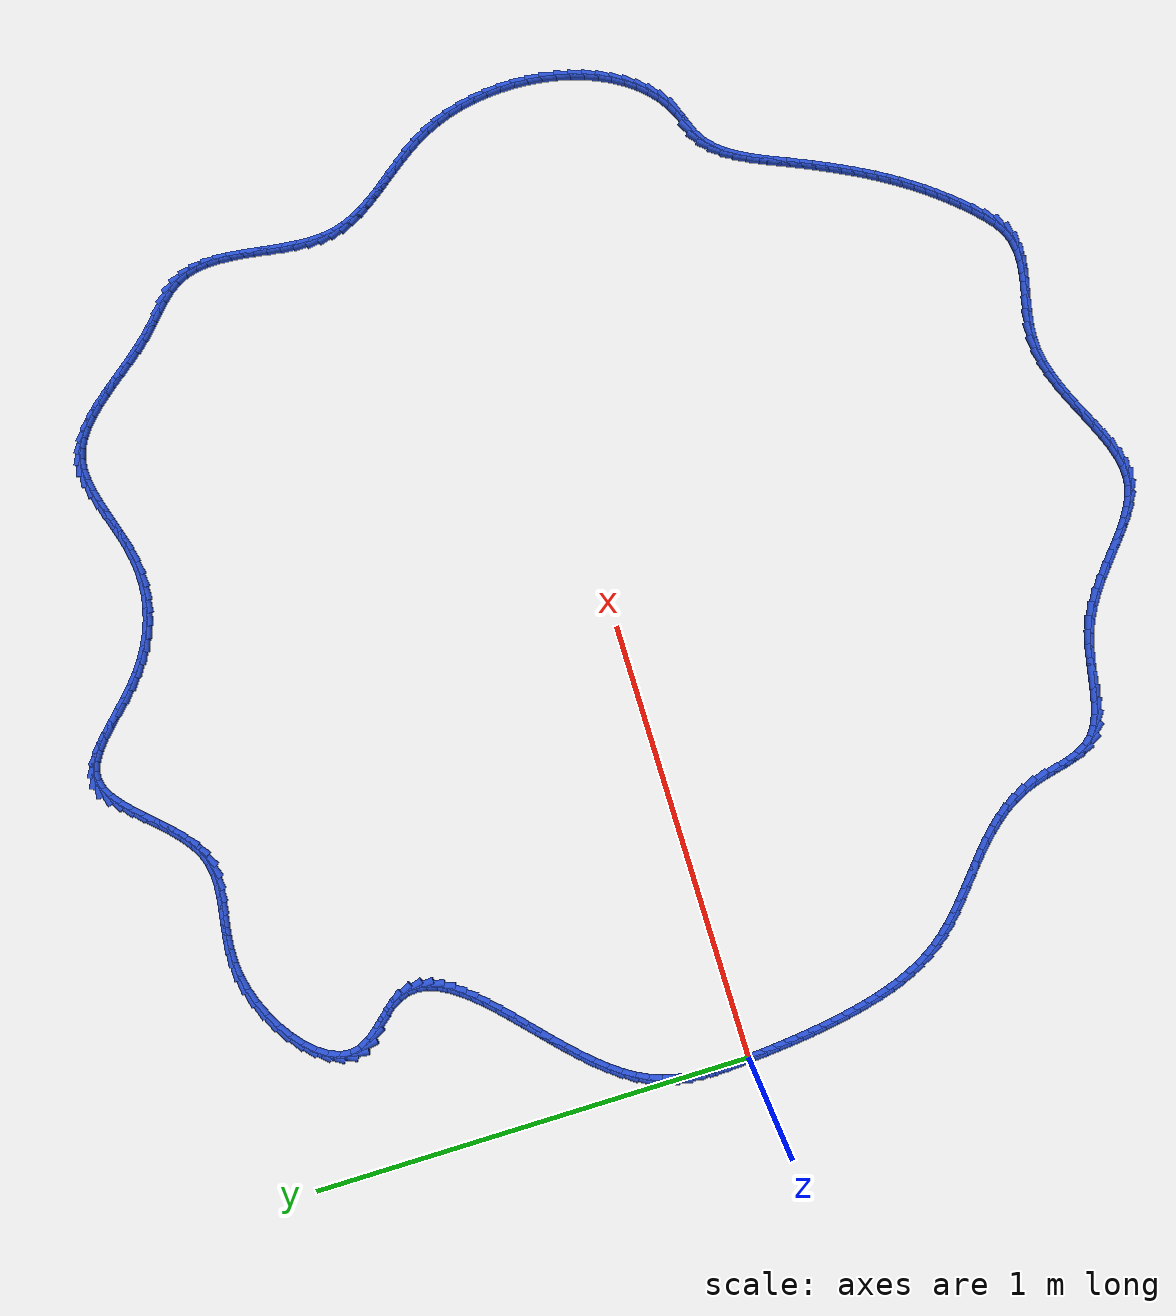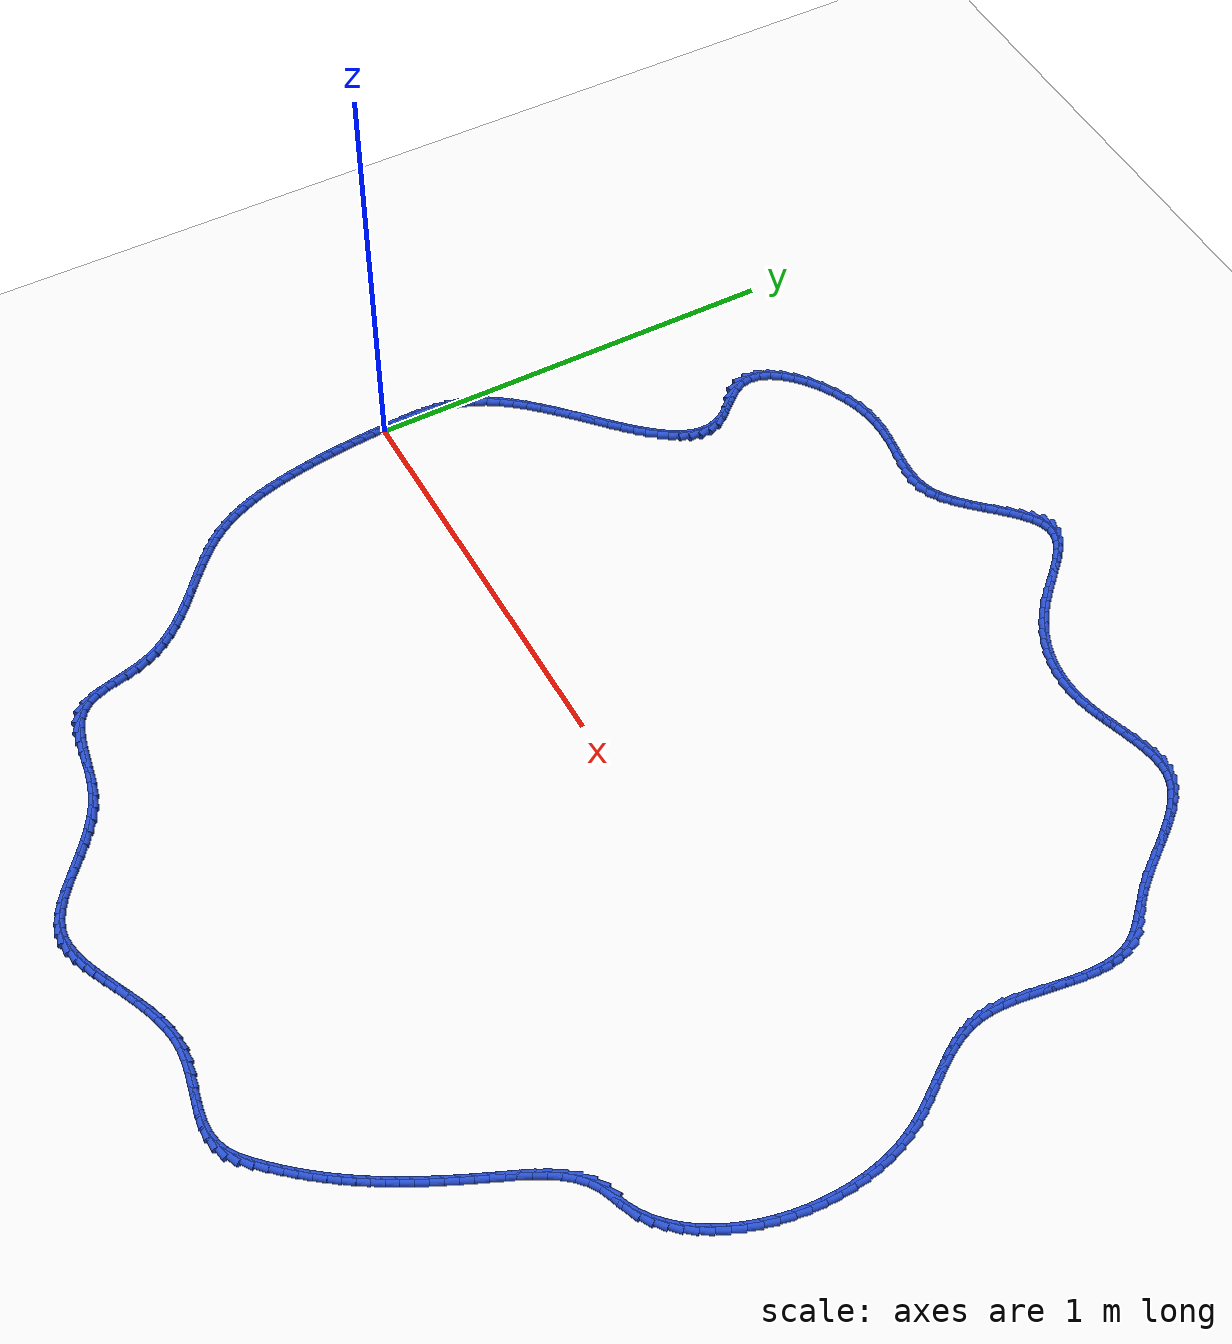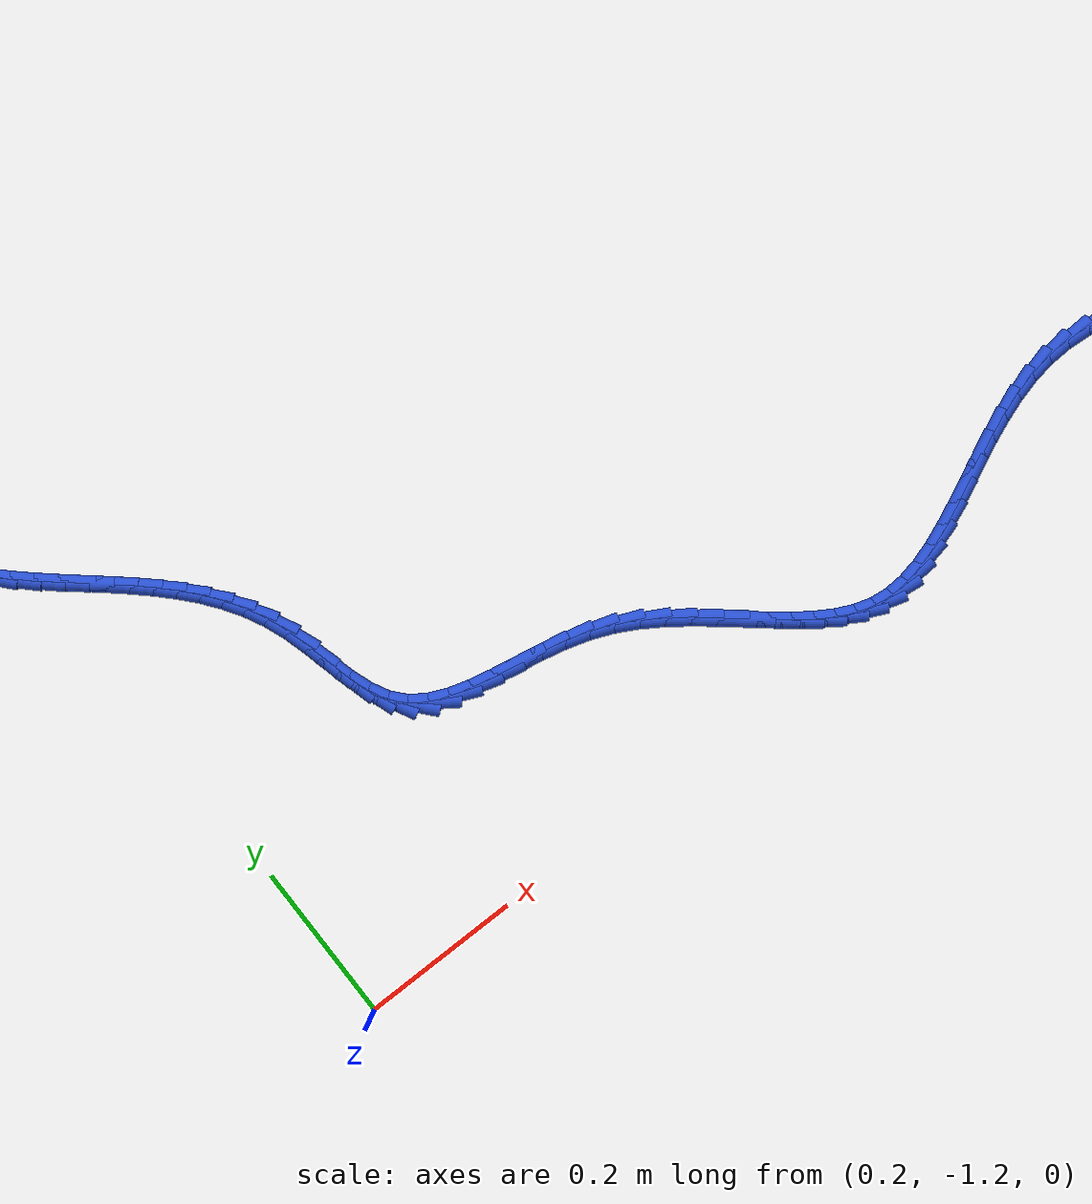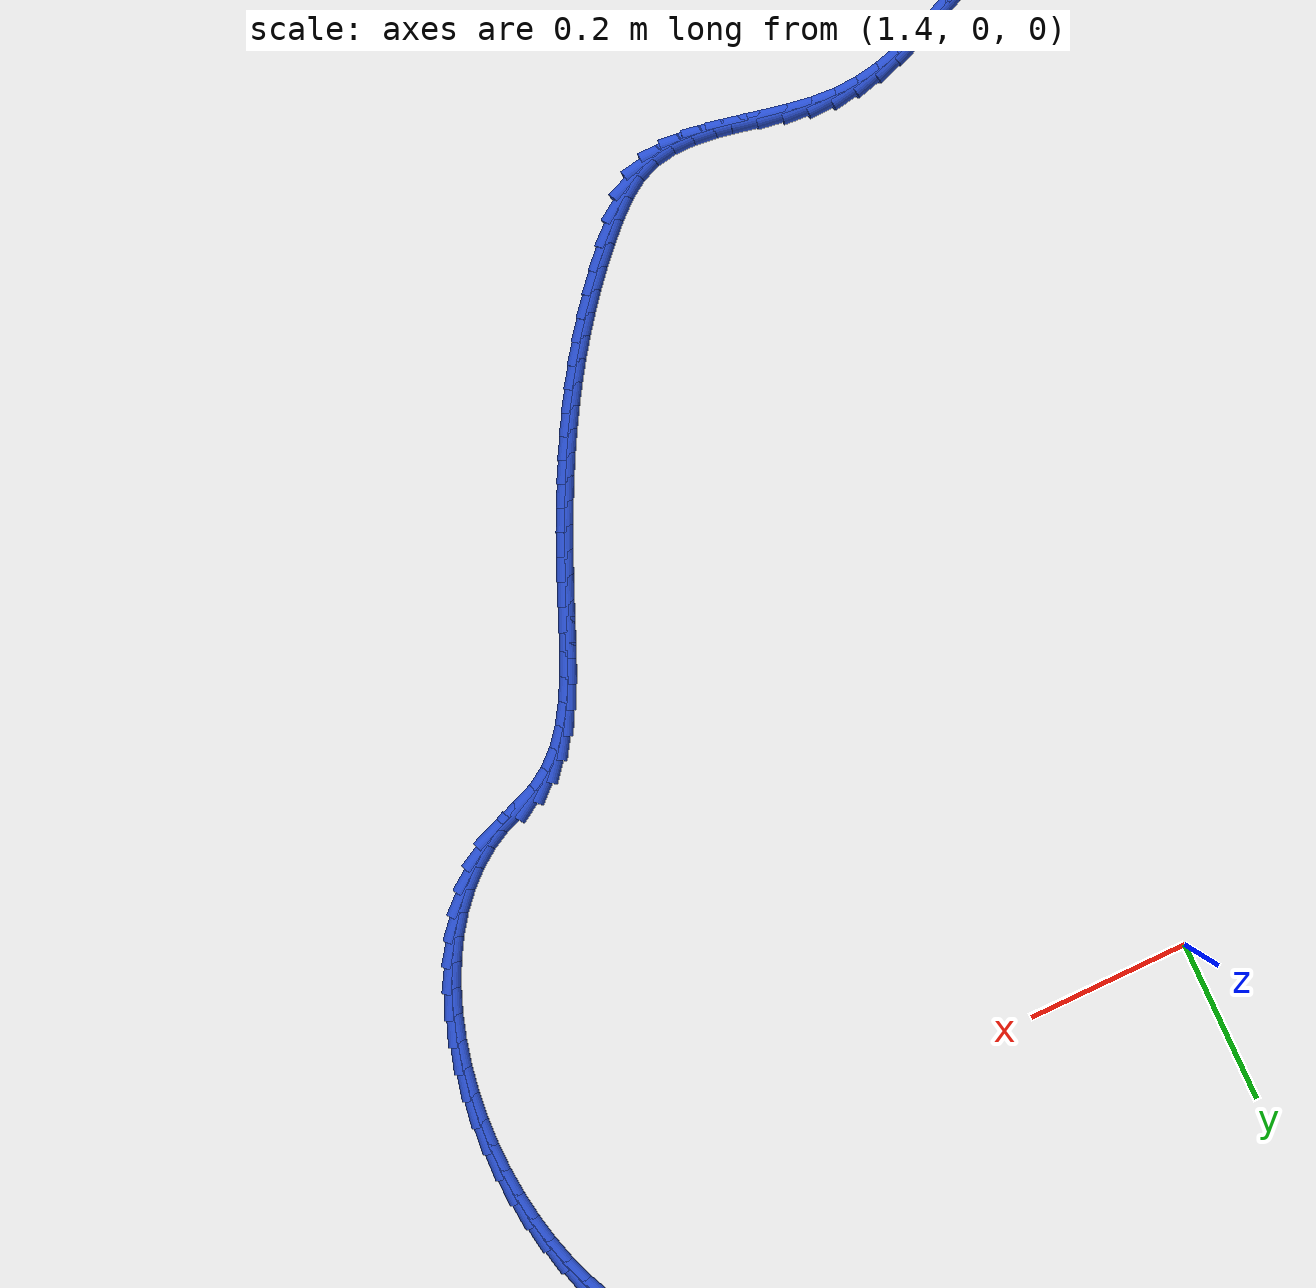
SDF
<sdf version="1.6">
 <world name="default">
  <light name="sun" type="directional">
   <pose>0 0 10 0 -0 0</pose>
   <diffuse>0.8 0.8 0.8 1</diffuse>
   <specular>0.2 0.2 0.2 1</specular>
   <attenuation>
    <range>1000</range>
    <constant>0.9</constant>
    <linear>0.01</linear>
    <quadratic>0.001</quadratic>
   </attenuation>
   <direction>-0.5 0.1 -0.9</direction>
  </light>
  <model name="ground_plane">
   <static>1</static>
   <link name="link">
    <collision name="collision">
     <geometry><plane><normal>0 0 1</normal><size>100 100</size></plane></geometry>
     <surface><friction><ode><mu>100</mu><mu2>50</mu2></ode></friction></surface>
    </collision>
    <visual name="visual">
     <cast_shadows>0</cast_shadows>
     <geometry><plane><normal>0 0 1</normal><size>100 100</size></plane></geometry>
     <material>
      <script><uri>file://media/materials/scripts/gazebo.material</uri><name>Gazebo/WhiteGlow</name></script>
     </material>
    </visual>
   </link>
  </model>
  <gravity>0 0 -9.8</gravity>
  <magnetic_field>6e-06 2.3e-05 -4.2e-05</magnetic_field>
  <atmosphere type="adiabatic"/>
  <physics name="default_physics" default="0" type="ode">
   <max_step_size>0.001</max_step_size>
   <real_time_factor>1</real_time_factor>
   <real_time_update_rate>1000</real_time_update_rate>
  </physics>
  <scene><ambient>0.4 0.4 0.4 1</ambient><background>0.7 0.7 0.7 1</background><shadows>1</shadows></scene>
  <spherical_coordinates>
   <surface_model>EARTH_WGS84</surface_model>
   <latitude_deg>0</latitude_deg>
   <longitude_deg>0</longitude_deg>
   <elevation>0</elevation>
   <heading_deg>0</heading_deg>
  </spherical_coordinates>
  <model name="line">
   <link name="link_0">
    <pose>-3.903127820947816e-18 -3.469446951953614e-17 0.01 0 1.57 -1.507361087501564</pose>
    <collision name="collision">
     <geometry><cylinder><radius>0.01</radius><length>0.08</length></cylinder></geometry>
    </collision>
    <visual name="visual">
     <material>
      <script><name>Gazebo/Blue</name><uri>file://media/materials/scripts/gazebo.material</uri></script>
     </material>
     <geometry><cylinder><radius>0.01</radius><length>0.08</length></cylinder></geometry>
    </visual>
   </link>
   <link name="link_1">
    <pose>-0.0018077059022607862 0.02845863777967326 0.01 0 1.57 -1.527354065004989</pose>
    <collision name="collision">
     <geometry><cylinder><radius>0.01</radius><length>0.08</length></cylinder></geometry>
    </collision>
    <visual name="visual">
     <material>
      <script><name>Gazebo/Blue</name><uri>file://media/materials/scripts/gazebo.material</uri></script>
     </material>
     <geometry><cylinder><radius>0.01</radius><length>0.08</length></cylinder></geometry>
    </visual>
   </link>
   <link name="link_2">
    <pose>-0.0030477444912490013 0.05698520063292673 0.01 0 1.57 -1.5605273810109488</pose>
    <collision name="collision">
     <geometry><cylinder><radius>0.01</radius><length>0.08</length></cylinder></geometry>
    </collision>
    <visual name="visual">
     <material>
      <script><name>Gazebo/Blue</name><uri>file://media/materials/scripts/gazebo.material</uri></script>
     </material>
     <geometry><cylinder><radius>0.01</radius><length>0.08</length></cylinder></geometry>
    </visual>
   </link>
   <link name="link_3">
    <pose>-0.003340647359984815 0.08550736631264412 0.01 0 1.57 1.5344725306758564</pose>
    <collision name="collision">
     <geometry><cylinder><radius>0.01</radius><length>0.08</length></cylinder></geometry>
    </collision>
    <visual name="visual">
     <material>
      <script><name>Gazebo/Blue</name><uri>file://media/materials/scripts/gazebo.material</uri></script>
     </material>
     <geometry><cylinder><radius>0.01</radius><length>0.08</length></cylinder></geometry>
    </visual>
   </link>
   <link name="link_4">
    <pose>-0.002306946101488388 0.11395281257170907 0.01 0 1.57 1.4742731124760284</pose>
    <collision name="collision">
     <geometry><cylinder><radius>0.01</radius><length>0.08</length></cylinder></geometry>
    </collision>
    <visual name="visual">
     <material>
      <script><name>Gazebo/Blue</name><uri>file://media/materials/scripts/gazebo.material</uri></script>
     </material>
     <geometry><cylinder><radius>0.01</radius><length>0.08</length></cylinder></geometry>
    </visual>
   </link>
   <link name="link_5">
    <pose>0.0004328276912201074 0.14224921716300548 0.01 0 1.57 1.4005872689753363</pose>
    <collision name="collision">
     <geometry><cylinder><radius>0.01</radius><length>0.08</length></cylinder></geometry>
    </collision>
    <visual name="visual">
     <material>
      <script><name>Gazebo/Blue</name><uri>file://media/materials/scripts/gazebo.material</uri></script>
     </material>
     <geometry><cylinder><radius>0.01</radius><length>0.08</length></cylinder></geometry>
    </visual>
   </link>
   <link name="link_6">
    <pose>0.005258142425120512 0.17032425783941693 0.01 0 1.57 1.3141648265684118</pose>
    <collision name="collision">
     <geometry><cylinder><radius>0.01</radius><length>0.08</length></cylinder></geometry>
    </collision>
    <visual name="visual">
     <material>
      <script><name>Gazebo/Blue</name><uri>file://media/materials/scripts/gazebo.material</uri></script>
     </material>
     <geometry><cylinder><radius>0.01</radius><length>0.08</length></cylinder></geometry>
    </visual>
   </link>
   <link name="link_7">
    <pose>0.012548466507192654 0.19810561235382723 0.01 0 1.57 1.216701219416777</pose>
    <collision name="collision">
     <geometry><cylinder><radius>0.01</radius><length>0.08</length></cylinder></geometry>
    </collision>
    <visual name="visual">
     <material>
      <script><name>Gazebo/Blue</name><uri>file://media/materials/scripts/gazebo.material</uri></script>
     </material>
     <geometry><cylinder><radius>0.01</radius><length>0.08</length></cylinder></geometry>
    </visual>
   </link>
   <link name="link_8">
    <pose>0.02268326834441637 0.22552095845912012 0.01 0 1.57 1.111532479688611</pose>
    <collision name="collision">
     <geometry><cylinder><radius>0.01</radius><length>0.08</length></cylinder></geometry>
    </collision>
    <visual name="visual">
     <material>
      <script><name>Gazebo/Blue</name><uri>file://media/materials/scripts/gazebo.material</uri></script>
     </material>
     <geometry><cylinder><radius>0.01</radius><length>0.08</length></cylinder></geometry>
    </visual>
   </link>
   <link name="link_9">
    <pose>0.03602519263277827 0.2524998346841306 0.01 0 1.57 1.0139699110341625</pose>
    <collision name="collision">
     <geometry><cylinder><radius>0.01</radius><length>0.08</length></cylinder></geometry>
    </collision>
    <visual name="visual">
     <material>
      <script><name>Gazebo/Blue</name><uri>file://media/materials/scripts/gazebo.material</uri></script>
     </material>
     <geometry><cylinder><radius>0.01</radius><length>0.08</length></cylinder></geometry>
    </visual>
   </link>
   <link name="link_10">
    <pose>0.052532789469285676 0.27901647418613623 0.01 0 1.57 0.935639406556752</pose>
    <collision name="collision">
     <geometry><cylinder><radius>0.01</radius><length>0.08</length></cylinder></geometry>
    </collision>
    <visual name="visual">
     <material>
      <script><name>Gazebo/Blue</name><uri>file://media/materials/scripts/gazebo.material</uri></script>
     </material>
     <geometry><cylinder><radius>0.01</radius><length>0.08</length></cylinder></geometry>
    </visual>
   </link>
   <link name="link_11">
    <pose>0.07175075094101534 0.3050908846267712 0.01 0 1.57 0.8743194416370703</pose>
    <collision name="collision">
     <geometry><cylinder><radius>0.01</radius><length>0.08</length></cylinder></geometry>
    </collision>
    <visual name="visual">
     <material>
      <script><name>Gazebo/Blue</name><uri>file://media/materials/scripts/gazebo.material</uri></script>
     </material>
     <geometry><cylinder><radius>0.01</radius><length>0.08</length></cylinder></geometry>
    </visual>
   </link>
   <link name="link_12">
    <pose>0.09320499239296157 0.3307451504573942 0.01 0 1.57 0.827454178183127</pose>
    <collision name="collision">
     <geometry><cylinder><radius>0.01</radius><length>0.08</length></cylinder></geometry>
    </collision>
    <visual name="visual">
     <material>
      <script><name>Gazebo/Blue</name><uri>file://media/materials/scripts/gazebo.material</uri></script>
     </material>
     <geometry><cylinder><radius>0.01</radius><length>0.08</length></cylinder></geometry>
    </visual>
   </link>
   <link name="link_13">
    <pose>0.11642142917011872 0.3560013561293638 0.01 0 1.57 0.7930052700869376</pose>
    <collision name="collision">
     <geometry><cylinder><radius>0.01</radius><length>0.08</length></cylinder></geometry>
    </collision>
    <visual name="visual">
     <material>
      <script><name>Gazebo/Blue</name><uri>file://media/materials/scripts/gazebo.material</uri></script>
     </material>
     <geometry><cylinder><radius>0.01</radius><length>0.08</length></cylinder></geometry>
    </visual>
   </link>
   <link name="link_14">
    <pose>0.14092597661748107 0.3808815860940385 0.01 0 1.57 0.7695055071918945</pose>
    <collision name="collision">
     <geometry><cylinder><radius>0.01</radius><length>0.08</length></cylinder></geometry>
    </collision>
    <visual name="visual">
     <material>
      <script><name>Gazebo/Blue</name><uri>file://media/materials/scripts/gazebo.material</uri></script>
     </material>
     <geometry><cylinder><radius>0.01</radius><length>0.08</length></cylinder></geometry>
    </visual>
   </link>
   <link name="link_15">
    <pose>0.166244550080043 0.4054079248027767 0.01 0 1.57 0.7560406335067316</pose>
    <collision name="collision">
     <geometry><cylinder><radius>0.01</radius><length>0.08</length></cylinder></geometry>
    </collision>
    <visual name="visual">
     <material>
      <script><name>Gazebo/Blue</name><uri>file://media/materials/scripts/gazebo.material</uri></script>
     </material>
     <geometry><cylinder><radius>0.01</radius><length>0.08</length></cylinder></geometry>
    </visual>
   </link>
   <link name="link_16">
    <pose>0.19190306490279888 0.4296024567069374 0.01 0 1.57 0.7522269886127216</pose>
    <collision name="collision">
     <geometry><cylinder><radius>0.01</radius><length>0.08</length></cylinder></geometry>
    </collision>
    <visual name="visual">
     <material>
      <script><name>Gazebo/Blue</name><uri>file://media/materials/scripts/gazebo.material</uri></script>
     </material>
     <geometry><cylinder><radius>0.01</radius><length>0.08</length></cylinder></geometry>
    </visual>
   </link>
   <link name="link_17">
    <pose>0.21742743643074294 0.4534872662578789 0.01 0 1.57 0.7582170259758442</pose>
    <collision name="collision">
     <geometry><cylinder><radius>0.01</radius><length>0.08</length></cylinder></geometry>
    </collision>
    <visual name="visual">
     <material>
      <script><name>Gazebo/Blue</name><uri>file://media/materials/scripts/gazebo.material</uri></script>
     </material>
     <geometry><cylinder><radius>0.01</radius><length>0.08</length></cylinder></geometry>
    </visual>
   </link>
   <link name="link_18">
    <pose>0.24234358000886963 0.4770844379069597 0.01 0 1.57 0.774750670265783</pose>
    <collision name="collision">
     <geometry><cylinder><radius>0.01</radius><length>0.08</length></cylinder></geometry>
    </collision>
    <visual name="visual">
     <material>
      <script><name>Gazebo/Blue</name><uri>file://media/materials/scripts/gazebo.material</uri></script>
     </material>
     <geometry><cylinder><radius>0.01</radius><length>0.08</length></cylinder></geometry>
    </visual>
   </link>
   <link name="link_19">
    <pose>0.2661774109821732 0.5004160561055385 0.01 0 1.57 0.8032669781772184</pose>
    <collision name="collision">
     <geometry><cylinder><radius>0.01</radius><length>0.08</length></cylinder></geometry>
    </collision>
    <visual name="visual">
     <material>
      <script><name>Gazebo/Blue</name><uri>file://media/materials/scripts/gazebo.material</uri></script>
     </material>
     <geometry><cylinder><radius>0.01</radius><length>0.08</length></cylinder></geometry>
    </visual>
   </link>
   <link name="link_20">
    <pose>0.28845484469564797 0.5235042053049737 0.01 0 1.57 0.8460887213256204</pose>
    <collision name="collision">
     <geometry><cylinder><radius>0.01</radius><length>0.08</length></cylinder></geometry>
    </collision>
    <visual name="visual">
     <material>
      <script><name>Gazebo/Blue</name><uri>file://media/materials/scripts/gazebo.material</uri></script>
     </material>
     <geometry><cylinder><radius>0.01</radius><length>0.08</length></cylinder></geometry>
    </visual>
   </link>
   <link name="link_21">
    <pose>0.3087017964942883 0.546370969956624 0.01 0 1.57 0.9066782034397395</pose>
    <collision name="collision">
     <geometry><cylinder><radius>0.01</radius><length>0.08</length></cylinder></geometry>
    </collision>
    <visual name="visual">
     <material>
      <script><name>Gazebo/Blue</name><uri>file://media/materials/scripts/gazebo.material</uri></script>
     </material>
     <geometry><cylinder><radius>0.01</radius><length>0.08</length></cylinder></geometry>
    </visual>
   </link>
   <link name="link_22">
    <pose>0.32644418172308853 0.569038434511848 0.01 0 1.57 0.9898998767751676</pose>
    <collision name="collision">
     <geometry><cylinder><radius>0.01</radius><length>0.08</length></cylinder></geometry>
    </collision>
    <visual name="visual">
     <material>
      <script><name>Gazebo/Blue</name><uri>file://media/materials/scripts/gazebo.material</uri></script>
     </material>
     <geometry><cylinder><radius>0.01</radius><length>0.08</length></cylinder></geometry>
    </visual>
   </link>
   <link name="link_23">
    <pose>0.34120791572704295 0.5915286834220042 0.01 0 1.57 1.102024214414436</pose>
    <collision name="collision">
     <geometry><cylinder><radius>0.01</radius><length>0.08</length></cylinder></geometry>
    </collision>
    <visual name="visual">
     <material>
      <script><name>Gazebo/Blue</name><uri>file://media/materials/scripts/gazebo.material</uri></script>
     </material>
     <geometry><cylinder><radius>0.01</radius><length>0.08</length></cylinder></geometry>
    </visual>
   </link>
   <link name="link_24">
    <pose>0.35251891385114587 0.613863801138451 0.01 0 1.57 1.2497152944620502</pose>
    <collision name="collision">
     <geometry><cylinder><radius>0.01</radius><length>0.08</length></cylinder></geometry>
    </collision>
    <visual name="visual">
     <material>
      <script><name>Gazebo/Blue</name><uri>file://media/materials/scripts/gazebo.material</uri></script>
     </material>
     <geometry><cylinder><radius>0.01</radius><length>0.08</length></cylinder></geometry>
    </visual>
   </link>
   <link name="link_25">
    <pose>0.3599030914403919 0.6360658721125474 0.01 0 1.57 1.436564354704918</pose>
    <collision name="collision">
     <geometry><cylinder><radius>0.01</radius><length>0.08</length></cylinder></geometry>
    </collision>
    <visual name="visual">
     <material>
      <script><name>Gazebo/Blue</name><uri>file://media/materials/scripts/gazebo.material</uri></script>
     </material>
     <geometry><cylinder><radius>0.01</radius><length>0.08</length></cylinder></geometry>
    </visual>
   </link>
   <link name="link_26">
    <pose>0.3628863638397749 0.6581569807956513 0.01 0 1.57 -1.4850288130593812</pose>
    <collision name="collision">
     <geometry><cylinder><radius>0.01</radius><length>0.08</length></cylinder></geometry>
    </collision>
    <visual name="visual">
     <material>
      <script><name>Gazebo/Blue</name><uri>file://media/materials/scripts/gazebo.material</uri></script>
     </material>
     <geometry><cylinder><radius>0.01</radius><length>0.08</length></cylinder></geometry>
    </visual>
   </link>
   <link name="link_27">
    <pose>0.36099464639428946 0.6801592116391217 0.01 0 1.57 -1.2519625343550664</pose>
    <collision name="collision">
     <geometry><cylinder><radius>0.01</radius><length>0.08</length></cylinder></geometry>
    </collision>
    <visual name="visual">
     <material>
      <script><name>Gazebo/Blue</name><uri>file://media/materials/scripts/gazebo.material</uri></script>
     </material>
     <geometry><cylinder><radius>0.01</radius><length>0.08</length></cylinder></geometry>
    </visual>
   </link>
   <link name="link_28">
    <pose>0.3537538544489299 0.7020946490943174 0.01 0 1.57 -1.033050222345862</pose>
    <collision name="collision">
     <geometry><cylinder><radius>0.01</radius><length>0.08</length></cylinder></geometry>
    </collision>
    <visual name="visual">
     <material>
      <script><name>Gazebo/Blue</name><uri>file://media/materials/scripts/gazebo.material</uri></script>
     </material>
     <geometry><cylinder><radius>0.01</radius><length>0.08</length></cylinder></geometry>
    </visual>
   </link>
   <link name="link_29">
    <pose>0.34069861504387206 0.7239858231963666 0.01 0 1.57 -0.8807515365317208</pose>
    <collision name="collision">
     <geometry><cylinder><radius>0.01</radius><length>0.08</length></cylinder></geometry>
    </collision>
    <visual name="visual">
     <material>
      <script><name>Gazebo/Blue</name><uri>file://media/materials/scripts/gazebo.material</uri></script>
     </material>
     <geometry><cylinder><radius>0.01</radius><length>0.08</length></cylinder></geometry>
    </visual>
   </link>
   <link name="link_30">
    <pose>0.32259532627155973 0.745918266321278 0.01 0 1.57 -0.8399155517962795</pose>
    <collision name="collision">
     <geometry><cylinder><radius>0.01</radius><length>0.08</length></cylinder></geometry>
    </collision>
    <visual name="visual">
     <material>
      <script><name>Gazebo/Blue</name><uri>file://media/materials/scripts/gazebo.material</uri></script>
     </material>
     <geometry><cylinder><radius>0.01</radius><length>0.08</length></cylinder></geometry>
    </visual>
   </link>
   <link name="link_31">
    <pose>0.3027047282640937 0.7681050908747772 0.01 0 1.57 -0.8965930160381148</pose>
    <collision name="collision">
     <geometry><cylinder><radius>0.01</radius><length>0.08</length></cylinder></geometry>
    </collision>
    <visual name="visual">
     <material>
      <script><name>Gazebo/Blue</name><uri>file://media/materials/scripts/gazebo.material</uri></script>
     </material>
     <geometry><cylinder><radius>0.01</radius><length>0.08</length></cylinder></geometry>
    </visual>
   </link>
   <link name="link_32">
    <pose>0.2845889220684786 0.7907748232009614 0.01 0 1.57 -1.0706021516177606</pose>
    <collision name="collision">
     <geometry><cylinder><radius>0.01</radius><length>0.08</length></cylinder></geometry>
    </collision>
    <visual name="visual">
     <material>
      <script><name>Gazebo/Blue</name><uri>file://media/materials/scripts/gazebo.material</uri></script>
     </material>
     <geometry><cylinder><radius>0.01</radius><length>0.08</length></cylinder></geometry>
    </visual>
   </link>
   <link name="link_33">
    <pose>0.271809850574127 0.814155964805094 0.01 0 1.57 -1.3764358824852463</pose>
    <collision name="collision">
     <geometry><cylinder><radius>0.01</radius><length>0.08</length></cylinder></geometry>
    </collision>
    <visual name="visual">
     <material>
      <script><name>Gazebo/Blue</name><uri>file://media/materials/scripts/gazebo.material</uri></script>
     </material>
     <geometry><cylinder><radius>0.01</radius><length>0.08</length></cylinder></geometry>
    </visual>
   </link>
   <link name="link_34">
    <pose>0.26704956531521407 0.838338829224721 0.01 0 1.57 1.4496252330126995</pose>
    <collision name="collision">
     <geometry><cylinder><radius>0.01</radius><length>0.08</length></cylinder></geometry>
    </collision>
    <visual name="visual">
     <material>
      <script><name>Gazebo/Blue</name><uri>file://media/materials/scripts/gazebo.material</uri></script>
     </material>
     <geometry><cylinder><radius>0.01</radius><length>0.08</length></cylinder></geometry>
    </visual>
   </link>
   <link name="link_35">
    <pose>0.2700465850829104 0.8629514447331414 0.01 0 1.57 1.1885897428334957</pose>
    <collision name="collision">
     <geometry><cylinder><radius>0.01</radius><length>0.08</length></cylinder></geometry>
    </collision>
    <visual name="visual">
     <material>
      <script><name>Gazebo/Blue</name><uri>file://media/materials/scripts/gazebo.material</uri></script>
     </material>
     <geometry><cylinder><radius>0.01</radius><length>0.08</length></cylinder></geometry>
    </visual>
   </link>
   <link name="link_36">
    <pose>0.2799246189306106 0.8875252830143778 0.01 0 1.57 0.9874567396088259</pose>
    <collision name="collision">
     <geometry><cylinder><radius>0.01</radius><length>0.08</length></cylinder></geometry>
    </collision>
    <visual name="visual">
     <material>
      <script><name>Gazebo/Blue</name><uri>file://media/materials/scripts/gazebo.material</uri></script>
     </material>
     <geometry><cylinder><radius>0.01</radius><length>0.08</length></cylinder></geometry>
    </visual>
   </link>
   <link name="link_37">
    <pose>0.2958073759117091 0.9115918157524527 0.01 0 1.57 0.8325156610255934</pose>
    <collision name="collision">
     <geometry><cylinder><radius>0.01</radius><length>0.08</length></cylinder></geometry>
    </collision>
    <visual name="visual">
     <material>
      <script><name>Gazebo/Blue</name><uri>file://media/materials/scripts/gazebo.material</uri></script>
     </material>
     <geometry><cylinder><radius>0.01</radius><length>0.08</length></cylinder></geometry>
    </visual>
   </link>
   <link name="link_38">
    <pose>0.31681856507960054 0.9346825146313894 0.01 0 1.57 0.7084449168871932</pose>
    <collision name="collision">
     <geometry><cylinder><radius>0.01</radius><length>0.08</length></cylinder></geometry>
    </collision>
    <visual name="visual">
     <material>
      <script><name>Gazebo/Blue</name><uri>file://media/materials/scripts/gazebo.material</uri></script>
     </material>
     <geometry><cylinder><radius>0.01</radius><length>0.08</length></cylinder></geometry>
    </visual>
   </link>
   <link name="link_39">
    <pose>0.34208189548767937 0.9563288513352098 0.01 0 1.57 0.6033300780360683</pose>
    <collision name="collision">
     <geometry><cylinder><radius>0.01</radius><length>0.08</length></cylinder></geometry>
    </collision>
    <visual name="visual">
     <material>
      <script><name>Gazebo/Blue</name><uri>file://media/materials/scripts/gazebo.material</uri></script>
     </material>
     <geometry><cylinder><radius>0.01</radius><length>0.08</length></cylinder></geometry>
    </visual>
   </link>
   <link name="link_40">
    <pose>0.3707210761893398 0.9760622975479366 0.01 0 1.57 0.5083915146594752</pose>
    <collision name="collision">
     <geometry><cylinder><radius>0.01</radius><length>0.08</length></cylinder></geometry>
    </collision>
    <visual name="visual">
     <material>
      <script><name>Gazebo/Blue</name><uri>file://media/materials/scripts/gazebo.material</uri></script>
     </material>
     <geometry><cylinder><radius>0.01</radius><length>0.08</length></cylinder></geometry>
    </visual>
   </link>
   <link name="link_41">
    <pose>0.4018598162379765 0.9934143249535919 0.01 0 1.57 0.416724297669691</pose>
    <collision name="collision">
     <geometry><cylinder><radius>0.01</radius><length>0.08</length></cylinder></geometry>
    </collision>
    <visual name="visual">
     <material>
      <script><name>Gazebo/Blue</name><uri>file://media/materials/scripts/gazebo.material</uri></script>
     </material>
     <geometry><cylinder><radius>0.01</radius><length>0.08</length></cylinder></geometry>
    </visual>
   </link>
   <link name="link_42">
    <pose>0.4346218246869844 1.0079164052361997 0.01 0 1.57 0.3221249919168068</pose>
    <collision name="collision">
     <geometry><cylinder><radius>0.01</radius><length>0.08</length></cylinder></geometry>
    </collision>
    <visual name="visual">
     <material>
      <script><name>Gazebo/Blue</name><uri>file://media/materials/scripts/gazebo.material</uri></script>
     </material>
     <geometry><cylinder><radius>0.01</radius><length>0.08</length></cylinder></geometry>
    </visual>
   </link>
   <link name="link_43">
    <pose>0.4681308105897576 1.0191000100797818 0.01 0 1.57 0.21806637981734717</pose>
    <collision name="collision">
     <geometry><cylinder><radius>0.01</radius><length>0.08</length></cylinder></geometry>
    </collision>
    <visual name="visual">
     <material>
      <script><name>Gazebo/Blue</name><uri>file://media/materials/scripts/gazebo.material</uri></script>
     </material>
     <geometry><cylinder><radius>0.01</radius><length>0.08</length></cylinder></geometry>
    </visual>
   </link>
   <link name="link_44">
    <pose>0.5015104829996906 1.0264966111683604 0.01 0 1.57 0.10239759043898637</pose>
    <collision name="collision">
     <geometry><cylinder><radius>0.01</radius><length>0.08</length></cylinder></geometry>
    </collision>
    <visual name="visual">
     <material>
      <script><name>Gazebo/Blue</name><uri>file://media/materials/scripts/gazebo.material</uri></script>
     </material>
     <geometry><cylinder><radius>0.01</radius><length>0.08</length></cylinder></geometry>
    </visual>
   </link>
   <link name="link_45">
    <pose>0.5340093413587871 1.029836095919191 0.01 0 1.57 -0.0006746404395531789</pose>
    <collision name="collision">
     <geometry><cylinder><radius>0.01</radius><length>0.08</length></cylinder></geometry>
    </collision>
    <visual name="visual">
     <material>
      <script><name>Gazebo/Blue</name><uri>file://media/materials/scripts/gazebo.material</uri></script>
     </material>
     <geometry><cylinder><radius>0.01</radius><length>0.08</length></cylinder></geometry>
    </visual>
   </link>
   <link name="link_46">
    <pose>0.5654837562095326 1.0298148620029 0.01 0 1.57 -0.07827881950971081</pose>
    <collision name="collision">
     <geometry><cylinder><radius>0.01</radius><length>0.08</length></cylinder></geometry>
    </collision>
    <visual name="visual">
     <material>
      <script><name>Gazebo/Blue</name><uri>file://media/materials/scripts/gazebo.material</uri></script>
     </material>
     <geometry><cylinder><radius>0.01</radius><length>0.08</length></cylinder></geometry>
    </visual>
   </link>
   <link name="link_47">
    <pose>0.5959749140859301 1.0274231630583395 0.01 0 1.57 -0.12695988755573065</pose>
    <collision name="collision">
     <geometry><cylinder><radius>0.01</radius><length>0.08</length></cylinder></geometry>
    </collision>
    <visual name="visual">
     <material>
      <script><name>Gazebo/Blue</name><uri>file://media/materials/scripts/gazebo.material</uri></script>
     </material>
     <geometry><cylinder><radius>0.01</radius><length>0.08</length></cylinder></geometry>
    </visual>
   </link>
   <link name="link_48">
    <pose>0.625524044524338 1.023651321097768 0.01 0 1.57 -0.1442581065695643</pose>
    <collision name="collision">
     <geometry><cylinder><radius>0.01</radius><length>0.08</length></cylinder></geometry>
    </collision>
    <visual name="visual">
     <material>
      <script><name>Gazebo/Blue</name><uri>file://media/materials/scripts/gazebo.material</uri></script>
     </material>
     <geometry><cylinder><radius>0.01</radius><length>0.08</length></cylinder></geometry>
    </visual>
   </link>
   <link name="link_49">
    <pose>0.6541723770611149 1.0194896581334443 0.01 0 1.57 -0.12745644792053842</pose>
    <collision name="collision">
     <geometry><cylinder><radius>0.01</radius><length>0.08</length></cylinder></geometry>
    </collision>
    <visual name="visual">
     <material>
      <script><name>Gazebo/Blue</name><uri>file://media/materials/scripts/gazebo.material</uri></script>
     </material>
     <geometry><cylinder><radius>0.01</radius><length>0.08</length></cylinder></geometry>
    </visual>
   </link>
   <link name="link_50">
    <pose>0.6819611412326193 1.0159284961776254 0.01 0 1.57 -0.07292598415092778</pose>
    <collision name="collision">
     <geometry><cylinder><radius>0.01</radius><length>0.08</length></cylinder></geometry>
    </collision>
    <visual name="visual">
     <material>
      <script><name>Gazebo/Blue</name><uri>file://media/materials/scripts/gazebo.material</uri></script>
     </material>
     <geometry><cylinder><radius>0.01</radius><length>0.08</length></cylinder></geometry>
    </visual>
   </link>
   <link name="link_51">
    <pose>0.7089315665752096 1.0139581572425704 0.01 0 1.57 0.023314933380365513</pose>
    <collision name="collision">
     <geometry><cylinder><radius>0.01</radius><length>0.08</length></cylinder></geometry>
    </collision>
    <visual name="visual">
     <material>
      <script><name>Gazebo/Blue</name><uri>file://media/materials/scripts/gazebo.material</uri></script>
     </material>
     <geometry><cylinder><radius>0.01</radius><length>0.08</length></cylinder></geometry>
    </visual>
   </link>
   <link name="link_52">
    <pose>0.735124882625244 1.0145689633405375 0.01 0 1.57 0.16283042092886443</pose>
    <collision name="collision">
     <geometry><cylinder><radius>0.01</radius><length>0.08</length></cylinder></geometry>
    </collision>
    <visual name="visual">
     <material>
      <script><name>Gazebo/Blue</name><uri>file://media/materials/scripts/gazebo.material</uri></script>
     </material>
     <geometry><cylinder><radius>0.01</radius><length>0.08</length></cylinder></geometry>
    </visual>
   </link>
   <link name="link_53">
    <pose>0.7605823189190809 1.0187512364837845 0.01 0 1.57 0.3394454157202497</pose>
    <collision name="collision">
     <geometry><cylinder><radius>0.01</radius><length>0.08</length></cylinder></geometry>
    </collision>
    <visual name="visual">
     <material>
      <script><name>Gazebo/Blue</name><uri>file://media/materials/scripts/gazebo.material</uri></script>
     </material>
     <geometry><cylinder><radius>0.01</radius><length>0.08</length></cylinder></geometry>
    </visual>
   </link>
   <link name="link_54">
    <pose>0.7853451049930792 1.0274952986845696 0.01 0 1.57 0.5251894603597642</pose>
    <collision name="collision">
     <geometry><cylinder><radius>0.01</radius><length>0.08</length></cylinder></geometry>
    </collision>
    <visual name="visual">
     <material>
      <script><name>Gazebo/Blue</name><uri>file://media/materials/scripts/gazebo.material</uri></script>
     </material>
     <geometry><cylinder><radius>0.01</radius><length>0.08</length></cylinder></geometry>
    </visual>
   </link>
   <link name="link_55">
    <pose>0.8094586706737539 1.0414684621517336 0.01 0 1.57 0.6620279912062859</pose>
    <collision name="collision">
     <geometry><cylinder><radius>0.01</radius><length>0.08</length></cylinder></geometry>
    </collision>
    <visual name="visual">
     <material>
      <script><name>Gazebo/Blue</name><uri>file://media/materials/scripts/gazebo.material</uri></script>
     </material>
     <geometry><cylinder><radius>0.01</radius><length>0.08</length></cylinder></geometry>
    </visual>
   </link>
   <link name="link_56">
    <pose>0.832988360643213 1.0598065511847445 0.01 0 1.57 0.7486679545010145</pose>
    <collision name="collision">
     <geometry><cylinder><radius>0.01</radius><length>0.08</length></cylinder></geometry>
    </collision>
    <visual name="visual">
     <material>
      <script><name>Gazebo/Blue</name><uri>file://media/materials/scripts/gazebo.material</uri></script>
     </material>
     <geometry><cylinder><radius>0.01</radius><length>0.08</length></cylinder></geometry>
    </visual>
   </link>
   <link name="link_57">
    <pose>0.8560054157975348 1.08119196071419 0.01 0 1.57 0.7972029272546761</pose>
    <collision name="collision">
     <geometry><cylinder><radius>0.01</radius><length>0.08</length></cylinder></geometry>
    </collision>
    <visual name="visual">
     <material>
      <script><name>Gazebo/Blue</name><uri>file://media/materials/scripts/gazebo.material</uri></script>
     </material>
     <geometry><cylinder><radius>0.01</radius><length>0.08</length></cylinder></geometry>
    </visual>
   </link>
   <link name="link_58">
    <pose>0.8785810779382385 1.1043070160405464 0.01 0 1.57 0.8142867387462115</pose>
    <collision name="collision">
     <geometry><cylinder><radius>0.01</radius><length>0.08</length></cylinder></geometry>
    </collision>
    <visual name="visual">
     <material>
      <script><name>Gazebo/Blue</name><uri>file://media/materials/scripts/gazebo.material</uri></script>
     </material>
     <geometry><cylinder><radius>0.01</radius><length>0.08</length></cylinder></geometry>
    </visual>
   </link>
   <link name="link_59">
    <pose>0.9007865888668427 1.12783404246429 0.01 0 1.57 0.8014478657824622</pose>
    <collision name="collision">
     <geometry><cylinder><radius>0.01</radius><length>0.08</length></cylinder></geometry>
    </collision>
    <visual name="visual">
     <material>
      <script><name>Gazebo/Blue</name><uri>file://media/materials/scripts/gazebo.material</uri></script>
     </material>
     <geometry><cylinder><radius>0.01</radius><length>0.08</length></cylinder></geometry>
    </visual>
   </link>
   <link name="link_60">
    <pose>0.9226931903848674 1.1504553652858978 0.01 0 1.57 0.7549635422936344</pose>
    <collision name="collision">
     <geometry><cylinder><radius>0.01</radius><length>0.08</length></cylinder></geometry>
    </collision>
    <visual name="visual">
     <material>
      <script><name>Gazebo/Blue</name><uri>file://media/materials/scripts/gazebo.material</uri></script>
     </material>
     <geometry><cylinder><radius>0.01</radius><length>0.08</length></cylinder></geometry>
    </visual>
   </link>
   <link name="link_61">
    <pose>0.9443721242938319 1.1708533098058467 0.01 0 1.57 0.6644261017484699</pose>
    <collision name="collision">
     <geometry><cylinder><radius>0.01</radius><length>0.08</length></cylinder></geometry>
    </collision>
    <visual name="visual">
     <material>
      <script><name>Gazebo/Blue</name><uri>file://media/materials/scripts/gazebo.material</uri></script>
     </material>
     <geometry><cylinder><radius>0.01</radius><length>0.08</length></cylinder></geometry>
    </visual>
   </link>
   <link name="link_62">
    <pose>0.9658946323952552 1.1877102013246126 0.01 0 1.57 0.5102490264044575</pose>
    <collision name="collision">
     <geometry><cylinder><radius>0.01</radius><length>0.08</length></cylinder></geometry>
    </collision>
    <visual name="visual">
     <material>
      <script><name>Gazebo/Blue</name><uri>file://media/materials/scripts/gazebo.material</uri></script>
     </material>
     <geometry><cylinder><radius>0.01</radius><length>0.08</length></cylinder></geometry>
    </visual>
   </link>
   <link name="link_63">
    <pose>0.9873319564906566 1.1997083651426723 0.01 0 1.57 0.26534035609222084</pose>
    <collision name="collision">
     <geometry><cylinder><radius>0.01</radius><length>0.08</length></cylinder></geometry>
    </collision>
    <visual name="visual">
     <material>
      <script><name>Gazebo/Blue</name><uri>file://media/materials/scripts/gazebo.material</uri></script>
     </material>
     <geometry><cylinder><radius>0.01</radius><length>0.08</length></cylinder></geometry>
    </visual>
   </link>
   <link name="link_64">
    <pose>1.0087553383815557 1.2055301265605027 0.01 0 1.57 -0.06865727389634806</pose>
    <collision name="collision">
     <geometry><cylinder><radius>0.01</radius><length>0.08</length></cylinder></geometry>
    </collision>
    <visual name="visual">
     <material>
      <script><name>Gazebo/Blue</name><uri>file://media/materials/scripts/gazebo.material</uri></script>
     </material>
     <geometry><cylinder><radius>0.01</radius><length>0.08</length></cylinder></geometry>
    </visual>
   </link>
   <link name="link_65">
    <pose>1.0302363352045496 1.2040529781438092 0.01 0 1.57 -0.3663652059917775</pose>
    <collision name="collision">
     <geometry><cylinder><radius>0.01</radius><length>0.08</length></cylinder></geometry>
    </collision>
    <visual name="visual">
     <material>
      <script><name>Gazebo/Blue</name><uri>file://media/materials/scripts/gazebo.material</uri></script>
     </material>
     <geometry><cylinder><radius>0.01</radius><length>0.08</length></cylinder></geometry>
    </visual>
   </link>
   <link name="link_66">
    <pose>1.0518490989701217 1.1957604324525315 0.01 0 1.57 -0.5650890107931418</pose>
    <collision name="collision">
     <geometry><cylinder><radius>0.01</radius><length>0.08</length></cylinder></geometry>
    </collision>
    <visual name="visual">
     <material>
      <script><name>Gazebo/Blue</name><uri>file://media/materials/scripts/gazebo.material</uri></script>
     </material>
     <geometry><cylinder><radius>0.01</radius><length>0.08</length></cylinder></geometry>
    </visual>
   </link>
   <link name="link_67">
    <pose>1.0736690568654474 1.1819252347233482 0.01 0 1.57 -0.6861546189982555</pose>
    <collision name="collision">
     <geometry><cylinder><radius>0.01</radius><length>0.08</length></cylinder></geometry>
    </collision>
    <visual name="visual">
     <material>
      <script><name>Gazebo/Blue</name><uri>file://media/materials/scripts/gazebo.material</uri></script>
     </material>
     <geometry><cylinder><radius>0.01</radius><length>0.08</length></cylinder></geometry>
    </visual>
   </link>
   <link name="link_68">
    <pose>1.0957716449278216 1.163825607711318 0.01 0 1.57 -0.7538373123320089</pose>
    <collision name="collision">
     <geometry><cylinder><radius>0.01</radius><length>0.08</length></cylinder></geometry>
    </collision>
    <visual name="visual">
     <material>
      <script><name>Gazebo/Blue</name><uri>file://media/materials/scripts/gazebo.material</uri></script>
     </material>
     <geometry><cylinder><radius>0.01</radius><length>0.08</length></cylinder></geometry>
    </visual>
   </link>
   <link name="link_69">
    <pose>1.1182322991945388 1.1427397741714995 0.01 0 1.57 -0.7832019829565643</pose>
    <collision name="collision">
     <geometry><cylinder><radius>0.01</radius><length>0.08</length></cylinder></geometry>
    </collision>
    <visual name="visual">
     <material>
      <script><name>Gazebo/Blue</name><uri>file://media/materials/scripts/gazebo.material</uri></script>
     </material>
     <geometry><cylinder><radius>0.01</radius><length>0.08</length></cylinder></geometry>
    </visual>
   </link>
   <link name="link_70">
    <pose>1.141126455702895 1.1199459568589514 0.01 0 1.57 -0.781548101660726</pose>
    <collision name="collision">
     <geometry><cylinder><radius>0.01</radius><length>0.08</length></cylinder></geometry>
    </collision>
    <visual name="visual">
     <material>
      <script><name>Gazebo/Blue</name><uri>file://media/materials/scripts/gazebo.material</uri></script>
     </material>
     <geometry><cylinder><radius>0.01</radius><length>0.08</length></cylinder></geometry>
    </visual>
   </link>
   <link name="link_71">
    <pose>1.1645295504901843 1.0967223785287328 0.01 0 1.57 -0.7506351547629723</pose>
    <collision name="collision">
     <geometry><cylinder><radius>0.01</radius><length>0.08</length></cylinder></geometry>
    </collision>
    <visual name="visual">
     <material>
      <script><name>Gazebo/Blue</name><uri>file://media/materials/scripts/gazebo.material</uri></script>
     </material>
     <geometry><cylinder><radius>0.01</radius><length>0.08</length></cylinder></geometry>
    </visual>
   </link>
   <link name="link_72">
    <pose>1.1885170195937018 1.0743472619359025 0.01 0 1.57 -0.6893083918656042</pose>
    <collision name="collision">
     <geometry><cylinder><radius>0.01</radius><length>0.08</length></cylinder></geometry>
    </collision>
    <visual name="visual">
     <material>
      <script><name>Gazebo/Blue</name><uri>file://media/materials/scripts/gazebo.material</uri></script>
     </material>
     <geometry><cylinder><radius>0.01</radius><length>0.08</length></cylinder></geometry>
    </visual>
   </link>
   <link name="link_73">
    <pose>1.213158577444704 1.0540383293826272 0.01 0 1.57 -0.6118042056567816</pose>
    <collision name="collision">
     <geometry><cylinder><radius>0.01</radius><length>0.08</length></cylinder></geometry>
    </collision>
    <visual name="visual">
     <material>
      <script><name>Gazebo/Blue</name><uri>file://media/materials/scripts/gazebo.material</uri></script>
     </material>
     <geometry><cylinder><radius>0.01</radius><length>0.08</length></cylinder></geometry>
    </visual>
   </link>
   <link name="link_74">
    <pose>1.2384555158661643 1.036289800231295 0.01 0 1.57 -0.5297181678622142</pose>
    <collision name="collision">
     <geometry><cylinder><radius>0.01</radius><length>0.08</length></cylinder></geometry>
    </collision>
    <visual name="visual">
     <material>
      <script><name>Gazebo/Blue</name><uri>file://media/materials/scripts/gazebo.material</uri></script>
     </material>
     <geometry><cylinder><radius>0.01</radius><length>0.08</length></cylinder></geometry>
    </visual>
   </link>
   <link name="link_75">
    <pose>1.2643640593866377 1.021119350771493 0.01 0 1.57 -0.4436697737437152</pose>
    <collision name="collision">
     <geometry><cylinder><radius>0.01</radius><length>0.08</length></cylinder></geometry>
    </collision>
    <visual name="visual">
     <material>
      <script><name>Gazebo/Blue</name><uri>file://media/materials/scripts/gazebo.material</uri></script>
     </material>
     <geometry><cylinder><radius>0.01</radius><length>0.08</length></cylinder></geometry>
    </visual>
   </link>
   <link name="link_76">
    <pose>1.2908396388026537 1.008536264343943 0.01 0 1.57 -0.35428748753525774</pose>
    <collision name="collision">
     <geometry><cylinder><radius>0.01</radius><length>0.08</length></cylinder></geometry>
    </collision>
    <visual name="visual">
     <material>
      <script><name>Gazebo/Blue</name><uri>file://media/materials/scripts/gazebo.material</uri></script>
     </material>
     <geometry><cylinder><radius>0.01</radius><length>0.08</length></cylinder></geometry>
    </visual>
   </link>
   <link name="link_77">
    <pose>1.3178376849107436 0.9985498242893678 0.01 0 1.57 -0.2624225195902045</pose>
    <collision name="collision">
     <geometry><cylinder><radius>0.01</radius><length>0.08</length></cylinder></geometry>
    </collision>
    <visual name="visual">
     <material>
      <script><name>Gazebo/Blue</name><uri>file://media/materials/scripts/gazebo.material</uri></script>
     </material>
     <geometry><cylinder><radius>0.01</radius><length>0.08</length></cylinder></geometry>
    </visual>
   </link>
   <link name="link_78">
    <pose>1.3453136285074376 0.9911693139484881 0.01 0 1.57 -0.16911165839245496</pose>
    <collision name="collision">
     <geometry><cylinder><radius>0.01</radius><length>0.08</length></cylinder></geometry>
    </collision>
    <visual name="visual">
     <material>
      <script><name>Gazebo/Blue</name><uri>file://media/materials/scripts/gazebo.material</uri></script>
     </material>
     <geometry><cylinder><radius>0.01</radius><length>0.08</length></cylinder></geometry>
    </visual>
   </link>
   <link name="link_79">
    <pose>1.3732229003892666 0.9864040166620267 0.01 0 1.57 -0.07550810771967992</pose>
    <collision name="collision">
     <geometry><cylinder><radius>0.01</radius><length>0.08</length></cylinder></geometry>
    </collision>
    <visual name="visual">
     <material>
      <script><name>Gazebo/Blue</name><uri>file://media/materials/scripts/gazebo.material</uri></script>
     </material>
     <geometry><cylinder><radius>0.01</radius><length>0.08</length></cylinder></geometry>
    </visual>
   </link>
   <link name="link_80">
    <pose>1.4015209313527603 0.9842632157707054 0.01 0 1.57 0.017209914550818845</pose>
    <collision name="collision">
     <geometry><cylinder><radius>0.01</radius><length>0.08</length></cylinder></geometry>
    </collision>
    <visual name="visual">
     <material>
      <script><name>Gazebo/Blue</name><uri>file://media/materials/scripts/gazebo.material</uri></script>
     </material>
     <geometry><cylinder><radius>0.01</radius><length>0.08</length></cylinder></geometry>
    </visual>
   </link>
   <link name="link_81">
    <pose>1.43016315219445 0.9847561946152461 0.01 0 1.57 0.10793556669910466</pose>
    <collision name="collision">
     <geometry><cylinder><radius>0.01</radius><length>0.08</length></cylinder></geometry>
    </collision>
    <visual name="visual">
     <material>
      <script><name>Gazebo/Blue</name><uri>file://media/materials/scripts/gazebo.material</uri></script>
     </material>
     <geometry><cylinder><radius>0.01</radius><length>0.08</length></cylinder></geometry>
    </visual>
   </link>
   <link name="link_82">
    <pose>1.4591049937108662 0.9878922365363711 0.01 0 1.57 0.1931952816036505</pose>
    <collision name="collision">
     <geometry><cylinder><radius>0.01</radius><length>0.08</length></cylinder></geometry>
    </collision>
    <visual name="visual">
     <material>
      <script><name>Gazebo/Blue</name><uri>file://media/materials/scripts/gazebo.material</uri></script>
     </material>
     <geometry><cylinder><radius>0.01</radius><length>0.08</length></cylinder></geometry>
    </visual>
   </link>
   <link name="link_83">
    <pose>1.4882885850385599 0.9936015786839131 0.01 0 1.57 0.2560034183134011</pose>
    <collision name="collision">
     <geometry><cylinder><radius>0.01</radius><length>0.08</length></cylinder></geometry>
    </collision>
    <visual name="visual">
     <material>
      <script><name>Gazebo/Blue</name><uri>file://media/materials/scripts/gazebo.material</uri></script>
     </material>
     <geometry><cylinder><radius>0.01</radius><length>0.08</length></cylinder></geometry>
    </visual>
   </link>
   <link name="link_84">
    <pose>1.5175634558104536 1.0012641781636127 0.01 0 1.57 0.2917384775782794</pose>
    <collision name="collision">
     <geometry><cylinder><radius>0.01</radius><length>0.08</length></cylinder></geometry>
    </collision>
    <visual name="visual">
     <material>
      <script><name>Gazebo/Blue</name><uri>file://media/materials/scripts/gazebo.material</uri></script>
     </material>
     <geometry><cylinder><radius>0.01</radius><length>0.08</length></cylinder></geometry>
    </visual>
   </link>
   <link name="link_85">
    <pose>1.5467397651882988 1.0100260298701536 0.01 0 1.57 0.3022166279267805</pose>
    <collision name="collision">
     <geometry><cylinder><radius>0.01</radius><length>0.08</length></cylinder></geometry>
    </collision>
    <visual name="visual">
     <material>
      <script><name>Gazebo/Blue</name><uri>file://media/materials/scripts/gazebo.material</uri></script>
     </material>
     <geometry><cylinder><radius>0.01</radius><length>0.08</length></cylinder></geometry>
    </visual>
   </link>
   <link name="link_86">
    <pose>1.575627528010988 1.0190322710479394 0.01 0 1.57 0.28735045449923674</pose>
    <collision name="collision">
     <geometry><cylinder><radius>0.01</radius><length>0.08</length></cylinder></geometry>
    </collision>
    <visual name="visual">
     <material>
      <script><name>Gazebo/Blue</name><uri>file://media/materials/scripts/gazebo.material</uri></script>
     </material>
     <geometry><cylinder><radius>0.01</radius><length>0.08</length></cylinder></geometry>
    </visual>
   </link>
   <link name="link_87">
    <pose>1.6040367591174103 1.0274280389413712 0.01 0 1.57 0.24481761227179658</pose>
    <collision name="collision">
     <geometry><cylinder><radius>0.01</radius><length>0.08</length></cylinder></geometry>
    </collision>
    <visual name="visual">
     <material>
      <script><name>Gazebo/Blue</name><uri>file://media/materials/scripts/gazebo.material</uri></script>
     </material>
     <geometry><cylinder><radius>0.01</radius><length>0.08</length></cylinder></geometry>
    </visual>
   </link>
   <link name="link_88">
    <pose>1.6317774733464574 1.0343584707948512 0.01 0 1.57 0.1698452654842809</pose>
    <collision name="collision">
     <geometry><cylinder><radius>0.01</radius><length>0.08</length></cylinder></geometry>
    </collision>
    <visual name="visual">
     <material>
      <script><name>Gazebo/Blue</name><uri>file://media/materials/scripts/gazebo.material</uri></script>
     </material>
     <geometry><cylinder><radius>0.01</radius><length>0.08</length></cylinder></geometry>
    </visual>
   </link>
   <link name="link_89">
    <pose>1.6586596855370208 1.038968703852783 0.01 0 1.57 0.05549713772619637</pose>
    <collision name="collision">
     <geometry><cylinder><radius>0.01</radius><length>0.08</length></cylinder></geometry>
    </collision>
    <visual name="visual">
     <material>
      <script><name>Gazebo/Blue</name><uri>file://media/materials/scripts/gazebo.material</uri></script>
     </material>
     <geometry><cylinder><radius>0.01</radius><length>0.08</length></cylinder></geometry>
    </visual>
   </link>
   <link name="link_90">
    <pose>1.684493410527991 1.040403875359568 0.01 0 1.57 -0.10510836965926613</pose>
    <collision name="collision">
     <geometry><cylinder><radius>0.01</radius><length>0.08</length></cylinder></geometry>
    </collision>
    <visual name="visual">
     <material>
      <script><name>Gazebo/Blue</name><uri>file://media/materials/scripts/gazebo.material</uri></script>
     </material>
     <geometry><cylinder><radius>0.01</radius><length>0.08</length></cylinder></geometry>
    </visual>
   </link>
   <link name="link_91">
    <pose>1.7090886695151686 1.0378091454149923 0.01 0 1.57 -0.3005969065694672</pose>
    <collision name="collision">
     <geometry><cylinder><radius>0.01</radius><length>0.08</length></cylinder></geometry>
    </collision>
    <visual name="visual">
     <material>
      <script><name>Gazebo/Blue</name><uri>file://media/materials/scripts/gazebo.material</uri></script>
     </material>
     <geometry><cylinder><radius>0.01</radius><length>0.08</length></cylinder></geometry>
    </visual>
   </link>
   <link name="link_92">
    <pose>1.7323317844930175 1.0306040030363097 0.01 0 1.57 -0.47867323924218885</pose>
    <collision name="collision">
     <geometry><cylinder><radius>0.01</radius><length>0.08</length></cylinder></geometry>
    </collision>
    <visual name="visual">
     <material>
      <script><name>Gazebo/Blue</name><uri>file://media/materials/scripts/gazebo.material</uri></script>
     </material>
     <geometry><cylinder><radius>0.01</radius><length>0.08</length></cylinder></geometry>
    </visual>
   </link>
   <link name="link_93">
    <pose>1.7543752888416382 1.0191650632803104 0.01 0 1.57 -0.6217768013342018</pose>
    <collision name="collision">
     <geometry><cylinder><radius>0.01</radius><length>0.08</length></cylinder></geometry>
    </collision>
    <visual name="visual">
     <material>
      <script><name>Gazebo/Blue</name><uri>file://media/materials/scripts/gazebo.material</uri></script>
     </material>
     <geometry><cylinder><radius>0.01</radius><length>0.08</length></cylinder></geometry>
    </visual>
   </link>
   <link name="link_94">
    <pose>1.7754297387399853 1.004077554113169 0.01 0 1.57 -0.7301518663744101</pose>
    <collision name="collision">
     <geometry><cylinder><radius>0.01</radius><length>0.08</length></cylinder></geometry>
    </collision>
    <visual name="visual">
     <material>
      <script><name>Gazebo/Blue</name><uri>file://media/materials/scripts/gazebo.material</uri></script>
     </material>
     <geometry><cylinder><radius>0.01</radius><length>0.08</length></cylinder></geometry>
    </visual>
   </link>
   <link name="link_95">
    <pose>1.7957056903670119 0.9859267035010617 0.01 0 1.57 -0.808225720819763</pose>
    <collision name="collision">
     <geometry><cylinder><radius>0.01</radius><length>0.08</length></cylinder></geometry>
    </collision>
    <visual name="visual">
     <material>
      <script><name>Gazebo/Blue</name><uri>file://media/materials/scripts/gazebo.material</uri></script>
     </material>
     <geometry><cylinder><radius>0.01</radius><length>0.08</length></cylinder></geometry>
    </visual>
   </link>
   <link name="link_96">
    <pose>1.8154136999016717 0.9652977394101631 0.01 0 1.57 -0.8609891973935172</pose>
    <collision name="collision">
     <geometry><cylinder><radius>0.01</radius><length>0.08</length></cylinder></geometry>
    </collision>
    <visual name="visual">
     <material>
      <script><name>Gazebo/Blue</name><uri>file://media/materials/scripts/gazebo.material</uri></script>
     </material>
     <geometry><cylinder><radius>0.01</radius><length>0.08</length></cylinder></geometry>
    </visual>
   </link>
   <link name="link_97">
    <pose>1.8347643235229176 0.9427758898066483 0.01 0 1.57 -0.8924784905788519</pose>
    <collision name="collision">
     <geometry><cylinder><radius>0.01</radius><length>0.08</length></cylinder></geometry>
    </collision>
    <visual name="visual">
     <material>
      <script><name>Gazebo/Blue</name><uri>file://media/materials/scripts/gazebo.material</uri></script>
     </material>
     <geometry><cylinder><radius>0.01</radius><length>0.08</length></cylinder></geometry>
    </visual>
   </link>
   <link name="link_98">
    <pose>1.8539681174097045 0.9189463826566927 0.01 0 1.57 -0.905413803566667</pose>
    <collision name="collision">
     <geometry><cylinder><radius>0.01</radius><length>0.08</length></cylinder></geometry>
    </collision>
    <visual name="visual">
     <material>
      <script><name>Gazebo/Blue</name><uri>file://media/materials/scripts/gazebo.material</uri></script>
     </material>
     <geometry><cylinder><radius>0.01</radius><length>0.08</length></cylinder></geometry>
    </visual>
   </link>
   <link name="link_99">
    <pose>1.8732356377409853 0.8943944459264713 0.01 0 1.57 -0.9012511292822168</pose>
    <collision name="collision">
     <geometry><cylinder><radius>0.01</radius><length>0.08</length></cylinder></geometry>
    </collision>
    <visual name="visual">
     <material>
      <script><name>Gazebo/Blue</name><uri>file://media/materials/scripts/gazebo.material</uri></script>
     </material>
     <geometry><cylinder><radius>0.01</radius><length>0.08</length></cylinder></geometry>
    </visual>
   </link>
   <link name="link_100">
    <pose>1.8927774406957143 0.8697053075821604 0.01 0 1.57 -0.880316148188036</pose>
    <collision name="collision">
     <geometry><cylinder><radius>0.01</radius><length>0.08</length></cylinder></geometry>
    </collision>
    <visual name="visual">
     <material>
      <script><name>Gazebo/Blue</name><uri>file://media/materials/scripts/gazebo.material</uri></script>
     </material>
     <geometry><cylinder><radius>0.01</radius><length>0.08</length></cylinder></geometry>
    </visual>
   </link>
   <link name="link_101">
    <pose>1.912804082452844 0.845464195589934 0.01 0 1.57 -0.8419239726850981</pose>
    <collision name="collision">
     <geometry><cylinder><radius>0.01</radius><length>0.08</length></cylinder></geometry>
    </collision>
    <visual name="visual">
     <material>
      <script><name>Gazebo/Blue</name><uri>file://media/materials/scripts/gazebo.material</uri></script>
     </material>
     <geometry><cylinder><radius>0.01</radius><length>0.08</length></cylinder></geometry>
    </visual>
   </link>
   <link name="link_102">
    <pose>1.9335261191913293 0.8222563379159677 0.01 0 1.57 -0.7876854189831398</pose>
    <collision name="collision">
     <geometry><cylinder><radius>0.01</radius><length>0.08</length></cylinder></geometry>
    </collision>
    <visual name="visual">
     <material>
      <script><name>Gazebo/Blue</name><uri>file://media/materials/scripts/gazebo.material</uri></script>
     </material>
     <geometry><cylinder><radius>0.01</radius><length>0.08</length></cylinder></geometry>
    </visual>
   </link>
   <link name="link_103">
    <pose>1.9550854565618343 0.8005981508489145 0.01 0 1.57 -0.7538005368346232</pose>
    <collision name="collision">
     <geometry><cylinder><radius>0.01</radius><length>0.08</length></cylinder></geometry>
    </collision>
    <visual name="visual">
     <material>
      <script><name>Gazebo/Blue</name><uri>file://media/materials/scripts/gazebo.material</uri></script>
     </material>
     <geometry><cylinder><radius>0.01</radius><length>0.08</length></cylinder></geometry>
    </visual>
   </link>
   <link name="link_104">
    <pose>1.9768175906498278 0.7801977481583474 0.01 0 1.57 -0.7668100335997322</pose>
    <collision name="collision">
     <geometry><cylinder><radius>0.01</radius><length>0.08</length></cylinder></geometry>
    </collision>
    <visual name="visual">
     <material>
      <script><name>Gazebo/Blue</name><uri>file://media/materials/scripts/gazebo.material</uri></script>
     </material>
     <geometry><cylinder><radius>0.01</radius><length>0.08</length></cylinder></geometry>
    </visual>
   </link>
   <link name="link_105">
    <pose>1.997533762119092 0.7602377575627354 0.01 0 1.57 -0.8328126502563499</pose>
    <collision name="collision">
     <geometry><cylinder><radius>0.01</radius><length>0.08</length></cylinder></geometry>
    </collision>
    <visual name="visual">
     <material>
      <script><name>Gazebo/Blue</name><uri>file://media/materials/scripts/gazebo.material</uri></script>
     </material>
     <geometry><cylinder><radius>0.01</radius><length>0.08</length></cylinder></geometry>
    </visual>
   </link>
   <link name="link_106">
    <pose>2.0160362929661737 0.7398918671777631 0.01 0 1.57 -0.9600535271767279</pose>
    <collision name="collision">
     <geometry><cylinder><radius>0.01</radius><length>0.08</length></cylinder></geometry>
    </collision>
    <visual name="visual">
     <material>
      <script><name>Gazebo/Blue</name><uri>file://media/materials/scripts/gazebo.material</uri></script>
     </material>
     <geometry><cylinder><radius>0.01</radius><length>0.08</length></cylinder></geometry>
    </visual>
   </link>
   <link name="link_107">
    <pose>2.0311275051876203 0.7183337651191155 0.01 0 1.57 -1.140289312815464</pose>
    <collision name="collision">
     <geometry><cylinder><radius>0.01</radius><length>0.08</length></cylinder></geometry>
    </collision>
    <visual name="visual">
     <material>
      <script><name>Gazebo/Blue</name><uri>file://media/materials/scripts/gazebo.material</uri></script>
     </material>
     <geometry><cylinder><radius>0.01</radius><length>0.08</length></cylinder></geometry>
    </visual>
   </link>
   <link name="link_108">
    <pose>2.0418873715754677 0.6949037770842922 0.01 0 1.57 -1.3103490228393193</pose>
    <collision name="collision">
     <geometry><cylinder><radius>0.01</radius><length>0.08</length></cylinder></geometry>
    </collision>
    <visual name="visual">
     <material>
      <script><name>Gazebo/Blue</name><uri>file://media/materials/scripts/gazebo.material</uri></script>
     </material>
     <geometry><cylinder><radius>0.01</radius><length>0.08</length></cylinder></geometry>
    </visual>
   </link>
   <link name="link_109">
    <pose>2.048611675224627 0.6696719212193839 0.01 0 1.57 -1.4474818775757246</pose>
    <collision name="collision">
     <geometry><cylinder><radius>0.01</radius><length>0.08</length></cylinder></geometry>
    </collision>
    <visual name="visual">
     <material>
      <script><name>Gazebo/Blue</name><uri>file://media/materials/scripts/gazebo.material</uri></script>
     </material>
     <geometry><cylinder><radius>0.01</radius><length>0.08</length></cylinder></geometry>
    </visual>
   </link>
   <link name="link_110">
    <pose>2.051928898273188 0.6429078915400556 0.01 0 1.57 -1.5515799942879418</pose>
    <collision name="collision">
     <geometry><cylinder><radius>0.01</radius><length>0.08</length></cylinder></geometry>
    </collision>
    <visual name="visual">
     <material>
      <script><name>Gazebo/Blue</name><uri>file://media/materials/scripts/gazebo.material</uri></script>
     </material>
     <geometry><cylinder><radius>0.01</radius><length>0.08</length></cylinder></geometry>
    </visual>
   </link>
   <link name="link_111">
    <pose>2.0524675312035914 0.6148813870699993 0.01 0 1.57 1.515322402773047</pose>
    <collision name="collision">
     <geometry><cylinder><radius>0.01</radius><length>0.08</length></cylinder></geometry>
    </collision>
    <visual name="visual">
     <material>
      <script><name>Gazebo/Blue</name><uri>file://media/materials/scripts/gazebo.material</uri></script>
     </material>
     <geometry><cylinder><radius>0.01</radius><length>0.08</length></cylinder></geometry>
    </visual>
   </link>
   <link name="link_112">
    <pose>2.0508560644982783 0.5858621068329057 0.01 0 1.57 1.46584285747895</pose>
    <collision name="collision">
     <geometry><cylinder><radius>0.01</radius><length>0.08</length></cylinder></geometry>
    </collision>
    <visual name="visual">
     <material>
      <script><name>Gazebo/Blue</name><uri>file://media/materials/scripts/gazebo.material</uri></script>
     </material>
     <geometry><cylinder><radius>0.01</radius><length>0.08</length></cylinder></geometry>
    </visual>
   </link>
   <link name="link_113">
    <pose>2.0477229886396873 0.5561197498524661 0.01 0 1.57 1.438241652247419</pose>
    <collision name="collision">
     <geometry><cylinder><radius>0.01</radius><length>0.08</length></cylinder></geometry>
    </collision>
    <visual name="visual">
     <material>
      <script><name>Gazebo/Blue</name><uri>file://media/materials/scripts/gazebo.material</uri></script>
     </material>
     <geometry><cylinder><radius>0.01</radius><length>0.08</length></cylinder></geometry>
    </visual>
   </link>
   <link name="link_114">
    <pose>2.0436967941102613 0.5259240151523714 0.01 0 1.57 1.4304833205203604</pose>
    <collision name="collision">
     <geometry><cylinder><radius>0.01</radius><length>0.08</length></cylinder></geometry>
    </collision>
    <visual name="visual">
     <material>
      <script><name>Gazebo/Blue</name><uri>file://media/materials/scripts/gazebo.material</uri></script>
     </material>
     <geometry><cylinder><radius>0.01</radius><length>0.08</length></cylinder></geometry>
    </visual>
   </link>
   <link name="link_115">
    <pose>2.0394059713924397 0.4955446017563124 0.01 0 1.57 1.4418842857277208</pose>
    <collision name="collision">
     <geometry><cylinder><radius>0.01</radius><length>0.08</length></cylinder></geometry>
    </collision>
    <visual name="visual">
     <material>
      <script><name>Gazebo/Blue</name><uri>file://media/materials/scripts/gazebo.material</uri></script>
     </material>
     <geometry><cylinder><radius>0.01</radius><length>0.08</length></cylinder></geometry>
    </visual>
   </link>
   <link name="link_116">
    <pose>2.0354790109686633 0.4652512086879811 0.01 0 1.57 1.4730845856104966</pose>
    <collision name="collision">
     <geometry><cylinder><radius>0.01</radius><length>0.08</length></cylinder></geometry>
    </collision>
    <visual name="visual">
     <material>
      <script><name>Gazebo/Blue</name><uri>file://media/materials/scripts/gazebo.material</uri></script>
     </material>
     <geometry><cylinder><radius>0.01</radius><length>0.08</length></cylinder></geometry>
    </visual>
   </link>
   <link name="link_117">
    <pose>2.032544403321373 0.43531353497106823 0.01 0 1.57 1.5260066736077122</pose>
    <collision name="collision">
     <geometry><cylinder><radius>0.01</radius><length>0.08</length></cylinder></geometry>
    </collision>
    <visual name="visual">
     <material>
      <script><name>Gazebo/Blue</name><uri>file://media/materials/scripts/gazebo.material</uri></script>
     </material>
     <geometry><cylinder><radius>0.01</radius><length>0.08</length></cylinder></geometry>
    </visual>
   </link>
   <link name="link_118">
    <pose>2.031230638933009 0.40600127962926424 0.01 0 1.57 -1.5378854984170078</pose>
    <collision name="collision">
     <geometry><cylinder><radius>0.01</radius><length>0.08</length></cylinder></geometry>
    </collision>
    <visual name="visual">
     <material>
      <script><name>Gazebo/Blue</name><uri>file://media/materials/scripts/gazebo.material</uri></script>
     </material>
     <geometry><cylinder><radius>0.01</radius><length>0.08</length></cylinder></geometry>
    </visual>
   </link>
   <link name="link_119">
    <pose>2.0321662082860126 0.3775841416862616 0.01 0 1.57 -1.4317714088092721</pose>
    <collision name="collision">
     <geometry><cylinder><radius>0.01</radius><length>0.08</length></cylinder></geometry>
    </collision>
    <visual name="visual">
     <material>
      <script><name>Gazebo/Blue</name><uri>file://media/materials/scripts/gazebo.material</uri></script>
     </material>
     <geometry><cylinder><radius>0.01</radius><length>0.08</length></cylinder></geometry>
    </visual>
   </link>
   <link name="link_120">
    <pose>2.03597956247909 0.3503318012085993 0.01 0 1.57 -1.3035466312232742</pose>
    <collision name="collision">
     <geometry><cylinder><radius>0.01</radius><length>0.08</length></cylinder></geometry>
    </collision>
    <visual name="visual">
     <material>
      <script><name>Gazebo/Blue</name><uri>file://media/materials/scripts/gazebo.material</uri></script>
     </material>
     <geometry><cylinder><radius>0.01</radius><length>0.08</length></cylinder></geometry>
    </visual>
   </link>
   <link name="link_121">
    <pose>2.0430776681426175 0.32440732788857907 0.01 0 1.57 -1.1857007986821981</pose>
    <collision name="collision">
     <geometry><cylinder><radius>0.01</radius><length>0.08</length></cylinder></geometry>
    </collision>
    <visual name="visual">
     <material>
      <script><name>Gazebo/Blue</name><uri>file://media/materials/scripts/gazebo.material</uri></script>
     </material>
     <geometry><cylinder><radius>0.01</radius><length>0.08</length></cylinder></geometry>
    </visual>
   </link>
   <link name="link_122">
    <pose>2.0531260514534546 0.2996169029882652 0.01 0 1.57 -1.0890316122896848</pose>
    <collision name="collision">
     <geometry><cylinder><radius>0.01</radius><length>0.08</length></cylinder></geometry>
    </collision>
    <visual name="visual">
     <material>
      <script><name>Gazebo/Blue</name><uri>file://media/materials/scripts/gazebo.material</uri></script>
     </material>
     <geometry><cylinder><radius>0.01</radius><length>0.08</length></cylinder></geometry>
    </visual>
   </link>
   <link name="link_123">
    <pose>2.0656352690970006 0.275692114026853 0.01 0 1.57 -1.0152583380880218</pose>
    <collision name="collision">
     <geometry><cylinder><radius>0.01</radius><length>0.08</length></cylinder></geometry>
    </collision>
    <visual name="visual">
     <material>
      <script><name>Gazebo/Blue</name><uri>file://media/materials/scripts/gazebo.material</uri></script>
     </material>
     <geometry><cylinder><radius>0.01</radius><length>0.08</length></cylinder></geometry>
    </visual>
   </link>
   <link name="link_124">
    <pose>2.0801158777586544 0.25236454852353873 0.01 0 1.57 -0.9640668771519387</pose>
    <collision name="collision">
     <geometry><cylinder><radius>0.01</radius><length>0.08</length></cylinder></geometry>
    </collision>
    <visual name="visual">
     <material>
      <script><name>Gazebo/Blue</name><uri>file://media/materials/scripts/gazebo.material</uri></script>
     </material>
     <geometry><cylinder><radius>0.01</radius><length>0.08</length></cylinder></geometry>
    </visual>
   </link>
   <link name="link_125">
    <pose>2.0960784341238146 0.22936579399751778 0.01 0 1.57 -0.934270527627311</pose>
    <collision name="collision">
     <geometry><cylinder><radius>0.01</radius><length>0.08</length></cylinder></geometry>
    </collision>
    <visual name="visual">
     <material>
      <script><name>Gazebo/Blue</name><uri>file://media/materials/scripts/gazebo.material</uri></script>
     </material>
     <geometry><cylinder><radius>0.01</radius><length>0.08</length></cylinder></geometry>
    </visual>
   </link>
   <link name="link_126">
    <pose>2.113033494877882 0.2064274379679856 0.01 0 1.57 -0.9245815264626674</pose>
    <collision name="collision">
     <geometry><cylinder><radius>0.01</radius><length>0.08</length></cylinder></geometry>
    </collision>
    <visual name="visual">
     <material>
      <script><name>Gazebo/Blue</name><uri>file://media/materials/scripts/gazebo.material</uri></script>
     </material>
     <geometry><cylinder><radius>0.01</radius><length>0.08</length></cylinder></geometry>
    </visual>
   </link>
   <link name="link_127">
    <pose>2.1304916167062564 0.18328106795413848 0.01 0 1.57 -0.9339757741442324</pose>
    <collision name="collision">
     <geometry><cylinder><radius>0.01</radius><length>0.08</length></cylinder></geometry>
    </collision>
    <visual name="visual">
     <material>
      <script><name>Gazebo/Blue</name><uri>file://media/materials/scripts/gazebo.material</uri></script>
     </material>
     <geometry><cylinder><radius>0.01</radius><length>0.08</length></cylinder></geometry>
    </visual>
   </link>
   <link name="link_128">
    <pose>2.1479633562943348 0.1596582714751717 0.01 0 1.57 -0.9617643121148131</pose>
    <collision name="collision">
     <geometry><cylinder><radius>0.01</radius><length>0.08</length></cylinder></geometry>
    </collision>
    <visual name="visual">
     <material>
      <script><name>Gazebo/Blue</name><uri>file://media/materials/scripts/gazebo.material</uri></script>
     </material>
     <geometry><cylinder><radius>0.01</radius><length>0.08</length></cylinder></geometry>
    </visual>
   </link>
   <link name="link_129">
    <pose>2.1649592703275173 0.13529063605028108 0.01 0 1.57 -1.0074628464894861</pose>
    <collision name="collision">
     <geometry><cylinder><radius>0.01</radius><length>0.08</length></cylinder></geometry>
    </collision>
    <visual name="visual">
     <material>
      <script><name>Gazebo/Blue</name><uri>file://media/materials/scripts/gazebo.material</uri></script>
     </material>
     <geometry><cylinder><radius>0.01</radius><length>0.08</length></cylinder></geometry>
    </visual>
   </link>
   <link name="link_130">
    <pose>2.180989915491204 0.10990974919866221 0.01 0 1.57 -1.0705041970759233</pose>
    <collision name="collision">
     <geometry><cylinder><radius>0.01</radius><length>0.08</length></cylinder></geometry>
    </collision>
    <visual name="visual">
     <material>
      <script><name>Gazebo/Blue</name><uri>file://media/materials/scripts/gazebo.material</uri></script>
     </material>
     <geometry><cylinder><radius>0.01</radius><length>0.08</length></cylinder></geometry>
    </visual>
   </link>
   <link name="link_131">
    <pose>2.195565848470794 0.08324719843951087 0.01 0 1.57 -1.1485788876861844</pose>
    <collision name="collision">
     <geometry><cylinder><radius>0.01</radius><length>0.08</length></cylinder></geometry>
    </collision>
    <visual name="visual">
     <material>
      <script><name>Gazebo/Blue</name><uri>file://media/materials/scripts/gazebo.material</uri></script>
     </material>
     <geometry><cylinder><radius>0.01</radius><length>0.08</length></cylinder></geometry>
    </visual>
   </link>
   <link name="link_132">
    <pose>2.2082265251599895 0.05506444085726743 0.01 0 1.57 -1.2278576072758378</pose>
    <collision name="collision">
     <geometry><cylinder><radius>0.01</radius><length>0.08</length></cylinder></geometry>
    </collision>
    <visual name="visual">
     <material>
      <script><name>Gazebo/Blue</name><uri>file://media/materials/scripts/gazebo.material</uri></script>
     </material>
     <geometry><cylinder><radius>0.01</radius><length>0.08</length></cylinder></geometry>
    </visual>
   </link>
   <link name="link_133">
    <pose>2.218807699233438 0.02542918019222179 0.01 0 1.57 -1.3015198901947602</pose>
    <collision name="collision">
     <geometry><cylinder><radius>0.01</radius><length>0.08</length></cylinder></geometry>
    </collision>
    <visual name="visual">
     <material>
      <script><name>Gazebo/Blue</name><uri>file://media/materials/scripts/gazebo.material</uri></script>
     </material>
     <geometry><cylinder><radius>0.01</radius><length>0.08</length></cylinder></geometry>
    </visual>
   </link>
   <link name="link_134">
    <pose>2.227318997335612 -0.005411168663320669 0.01 0 1.57 -1.3705563075115206</pose>
    <collision name="collision">
     <geometry><cylinder><radius>0.01</radius><length>0.08</length></cylinder></geometry>
    </collision>
    <visual name="visual">
     <material>
      <script><name>Gazebo/Blue</name><uri>file://media/materials/scripts/gazebo.material</uri></script>
     </material>
     <geometry><cylinder><radius>0.01</radius><length>0.08</length></cylinder></geometry>
    </visual>
   </link>
   <link name="link_135">
    <pose>2.233772257733157 -0.03720690493461526 0.01 0 1.57 -1.4360223727104497</pose>
    <collision name="collision">
     <geometry><cylinder><radius>0.01</radius><length>0.08</length></cylinder></geometry>
    </collision>
    <visual name="visual">
     <material>
      <script><name>Gazebo/Blue</name><uri>file://media/materials/scripts/gazebo.material</uri></script>
     </material>
     <geometry><cylinder><radius>0.01</radius><length>0.08</length></cylinder></geometry>
    </visual>
   </link>
   <link name="link_136">
    <pose>2.2381793186927226 -0.06970832784691641 0.01 0 1.57 -1.4989274099464993</pose>
    <collision name="collision">
     <geometry><cylinder><radius>0.01</radius><length>0.08</length></cylinder></geometry>
    </collision>
    <visual name="visual">
     <material>
      <script><name>Gazebo/Blue</name><uri>file://media/materials/scripts/gazebo.material</uri></script>
     </material>
     <geometry><cylinder><radius>0.01</radius><length>0.08</length></cylinder></geometry>
    </visual>
   </link>
   <link name="link_137">
    <pose>2.2405520184809555 -0.10266573662547859 0.01 0 1.57 -1.560237675769672</pose>
    <collision name="collision">
     <geometry><cylinder><radius>0.01</radius><length>0.08</length></cylinder></geometry>
    </collision>
    <visual name="visual">
     <material>
      <script><name>Gazebo/Blue</name><uri>file://media/materials/scripts/gazebo.material</uri></script>
     </material>
     <geometry><cylinder><radius>0.01</radius><length>0.08</length></cylinder></geometry>
    </visual>
   </link>
   <link name="link_138">
    <pose>2.2409021953645034 -0.1358294304955563 0.01 0 1.57 1.52070258775959</pose>
    <collision name="collision">
     <geometry><cylinder><radius>0.01</radius><length>0.08</length></cylinder></geometry>
    </collision>
    <visual name="visual">
     <material>
      <script><name>Gazebo/Blue</name><uri>file://media/materials/scripts/gazebo.material</uri></script>
     </material>
     <geometry><cylinder><radius>0.01</radius><length>0.08</length></cylinder></geometry>
    </visual>
   </link>
   <link name="link_139">
    <pose>2.239241687610013 -0.16894970868240394 0.01 0 1.57 1.459781285372613</pose>
    <collision name="collision">
     <geometry><cylinder><radius>0.01</radius><length>0.08</length></cylinder></geometry>
    </collision>
    <visual name="visual">
     <material>
      <script><name>Gazebo/Blue</name><uri>file://media/materials/scripts/gazebo.material</uri></script>
     </material>
     <geometry><cylinder><radius>0.01</radius><length>0.08</length></cylinder></geometry>
    </visual>
   </link>
   <link name="link_140">
    <pose>2.2355823334841336 -0.20177687041127704 0.01 0 1.57 1.3976527885412355</pose>
    <collision name="collision">
     <geometry><cylinder><radius>0.01</radius><length>0.08</length></cylinder></geometry>
    </collision>
    <visual name="visual">
     <material>
      <script><name>Gazebo/Blue</name><uri>file://media/materials/scripts/gazebo.material</uri></script>
     </material>
     <geometry><cylinder><radius>0.01</radius><length>0.08</length></cylinder></geometry>
    </visual>
   </link>
   <link name="link_141">
    <pose>2.2299359712535094 -0.23406121490742798 0.01 0 1.57 1.3333458316637485</pose>
    <collision name="collision">
     <geometry><cylinder><radius>0.01</radius><length>0.08</length></cylinder></geometry>
    </collision>
    <visual name="visual">
     <material>
      <script><name>Gazebo/Blue</name><uri>file://media/materials/scripts/gazebo.material</uri></script>
     </material>
     <geometry><cylinder><radius>0.01</radius><length>0.08</length></cylinder></geometry>
    </visual>
   </link>
   <link name="link_142">
    <pose>2.222314439184792 -0.26555304139611247 0.01 0 1.57 1.2658375643757025</pose>
    <collision name="collision">
     <geometry><cylinder><radius>0.01</radius><length>0.08</length></cylinder></geometry>
    </collision>
    <visual name="visual">
     <material>
      <script><name>Gazebo/Blue</name><uri>file://media/materials/scripts/gazebo.material</uri></script>
     </material>
     <geometry><cylinder><radius>0.01</radius><length>0.08</length></cylinder></geometry>
    </visual>
   </link>
   <link name="link_143">
    <pose>2.2127295755446257 -0.2960026491025846 0.01 0 1.57 1.1940420772942522</pose>
    <collision name="collision">
     <geometry><cylinder><radius>0.01</radius><length>0.08</length></cylinder></geometry>
    </collision>
    <visual name="visual">
     <material>
      <script><name>Gazebo/Blue</name><uri>file://media/materials/scripts/gazebo.material</uri></script>
     </material>
     <geometry><cylinder><radius>0.01</radius><length>0.08</length></cylinder></geometry>
    </visual>
   </link>
   <link name="link_144">
    <pose>2.201193218599659 -0.32516033725209914 0.01 0 1.57 1.1168131200579923</pose>
    <collision name="collision">
     <geometry><cylinder><radius>0.01</radius><length>0.08</length></cylinder></geometry>
    </collision>
    <visual name="visual">
     <material>
      <script><name>Gazebo/Blue</name><uri>file://media/materials/scripts/gazebo.material</uri></script>
     </material>
     <geometry><cylinder><radius>0.01</radius><length>0.08</length></cylinder></geometry>
    </visual>
   </link>
   <link name="link_145">
    <pose>2.187717206616539 -0.35277640506991026 0.01 0 1.57 1.0329723993900366</pose>
    <collision name="collision">
     <geometry><cylinder><radius>0.01</radius><length>0.08</length></cylinder></geometry>
    </collision>
    <visual name="visual">
     <material>
      <script><name>Gazebo/Blue</name><uri>file://media/materials/scripts/gazebo.material</uri></script>
     </material>
     <geometry><cylinder><radius>0.01</radius><length>0.08</length></cylinder></geometry>
    </visual>
   </link>
   <link name="link_146">
    <pose>2.172313377861915 -0.37860115178127285 0.01 0 1.57 0.9413801155111661</pose>
    <collision name="collision">
     <geometry><cylinder><radius>0.01</radius><length>0.08</length></cylinder></geometry>
    </collision>
    <visual name="visual">
     <material>
      <script><name>Gazebo/Blue</name><uri>file://media/materials/scripts/gazebo.material</uri></script>
     </material>
     <geometry><cylinder><radius>0.01</radius><length>0.08</length></cylinder></geometry>
    </visual>
   </link>
   <link name="link_147">
    <pose>2.154993570602432 -0.402384876611441 0.01 0 1.57 0.8410681035401546</pose>
    <collision name="collision">
     <geometry><cylinder><radius>0.01</radius><length>0.08</length></cylinder></geometry>
    </collision>
    <visual name="visual">
     <material>
      <script><name>Gazebo/Blue</name><uri>file://media/materials/scripts/gazebo.material</uri></script>
     </material>
     <geometry><cylinder><radius>0.01</radius><length>0.08</length></cylinder></geometry>
    </visual>
   </link>
   <link name="link_148">
    <pose>2.1357696231047383 -0.42387787878566935 0.01 0 1.57 0.7314517043867289</pose>
    <collision name="collision">
     <geometry><cylinder><radius>0.01</radius><length>0.08</length></cylinder></geometry>
    </collision>
    <visual name="visual">
     <material>
      <script><name>Gazebo/Blue</name><uri>file://media/materials/scripts/gazebo.material</uri></script>
     </material>
     <geometry><cylinder><radius>0.01</radius><length>0.08</length></cylinder></geometry>
    </visual>
   </link>
   <link name="link_149">
    <pose>2.114653373635481 -0.44283045752921285 0.01 0 1.57 0.6126132982627707</pose>
    <collision name="collision">
     <geometry><cylinder><radius>0.01</radius><length>0.08</length></cylinder></geometry>
    </collision>
    <visual name="visual">
     <material>
      <script><name>Gazebo/Blue</name><uri>file://media/materials/scripts/gazebo.material</uri></script>
     </material>
     <geometry><cylinder><radius>0.01</radius><length>0.08</length></cylinder></geometry>
    </visual>
   </link>
   <link name="link_150">
    <pose>2.091656660461309 -0.45899291206732484 0.01 0 1.57 0.4855987031985873</pose>
    <collision name="collision">
     <geometry><cylinder><radius>0.01</radius><length>0.08</length></cylinder></geometry>
    </collision>
    <visual name="visual">
     <material>
      <script><name>Gazebo/Blue</name><uri>file://media/materials/scripts/gazebo.material</uri></script>
     </material>
     <geometry><cylinder><radius>0.01</radius><length>0.08</length></cylinder></geometry>
    </visual>
   </link>
   <link name="link_151">
    <pose>2.0667913218488683 -0.4721155416252603 0.01 0 1.57 0.3608742065344251</pose>
    <collision name="collision">
     <geometry><cylinder><radius>0.01</radius><length>0.08</length></cylinder></geometry>
    </collision>
    <visual name="visual">
     <material>
      <script><name>Gazebo/Blue</name><uri>file://media/materials/scripts/gazebo.material</uri></script>
     </material>
     <geometry><cylinder><radius>0.01</radius><length>0.08</length></cylinder></geometry>
    </visual>
   </link>
   <link name="link_152">
    <pose>2.040195545505194 -0.48215282069603077 0.01 0 1.57 0.3730879010487373</pose>
    <collision name="collision">
     <geometry><cylinder><radius>0.01</radius><length>0.08</length></cylinder></geometry>
    </collision>
    <visual name="visual">
     <material>
      <script><name>Gazebo/Blue</name><uri>file://media/materials/scripts/gazebo.material</uri></script>
     </material>
     <geometry><cylinder><radius>0.01</radius><length>0.08</length></cylinder></geometry>
    </visual>
   </link>
   <link name="link_153">
    <pose>2.0140631321214095 -0.4923815665705689 0.01 0 1.57 0.5574745956991313</pose>
    <collision name="collision">
     <geometry><cylinder><radius>0.01</radius><length>0.08</length></cylinder></geometry>
    </collision>
    <visual name="visual">
     <material>
      <script><name>Gazebo/Blue</name><uri>file://media/materials/scripts/gazebo.material</uri></script>
     </material>
     <geometry><cylinder><radius>0.01</radius><length>0.08</length></cylinder></geometry>
    </visual>
   </link>
   <link name="link_154">
    <pose>1.9909666674938629 -0.5067807579916709 0.01 0 1.57 0.739959898626104</pose>
    <collision name="collision">
     <geometry><cylinder><radius>0.01</radius><length>0.08</length></cylinder></geometry>
    </collision>
    <visual name="visual">
     <material>
      <script><name>Gazebo/Blue</name><uri>file://media/materials/scripts/gazebo.material</uri></script>
     </material>
     <geometry><cylinder><radius>0.01</radius><length>0.08</length></cylinder></geometry>
    </visual>
   </link>
   <link name="link_155">
    <pose>1.9708016726368174 -0.5251917209516849 0.01 0 1.57 0.8879039832765999</pose>
    <collision name="collision">
     <geometry><cylinder><radius>0.01</radius><length>0.08</length></cylinder></geometry>
    </collision>
    <visual name="visual">
     <material>
      <script><name>Gazebo/Blue</name><uri>file://media/materials/scripts/gazebo.material</uri></script>
     </material>
     <geometry><cylinder><radius>0.01</radius><length>0.08</length></cylinder></geometry>
    </visual>
   </link>
   <link name="link_156">
    <pose>1.9531214480725456 -0.5469264146910405 0.01 0 1.57 1.0001711423737298</pose>
    <collision name="collision">
     <geometry><cylinder><radius>0.01</radius><length>0.08</length></cylinder></geometry>
    </collision>
    <visual name="visual">
     <material>
      <script><name>Gazebo/Blue</name><uri>file://media/materials/scripts/gazebo.material</uri></script>
     </material>
     <geometry><cylinder><radius>0.01</radius><length>0.08</length></cylinder></geometry>
    </visual>
   </link>
   <link name="link_157">
    <pose>1.9374792943233217 -0.5712967984501656 0.01 0 1.57 1.0804102111523053</pose>
    <collision name="collision">
     <geometry><cylinder><radius>0.01</radius><length>0.08</length></cylinder></geometry>
    </collision>
    <visual name="visual">
     <material>
      <script><name>Gazebo/Blue</name><uri>file://media/materials/scripts/gazebo.material</uri></script>
     </material>
     <geometry><cylinder><radius>0.01</radius><length>0.08</length></cylinder></geometry>
    </visual>
   </link>
   <link name="link_158">
    <pose>1.9234285119114176 -0.5976148314694891 0.01 0 1.57 1.1330815491557191</pose>
    <collision name="collision">
     <geometry><cylinder><radius>0.01</radius><length>0.08</length></cylinder></geometry>
    </collision>
    <visual name="visual">
     <material>
      <script><name>Gazebo/Blue</name><uri>file://media/materials/scripts/gazebo.material</uri></script>
     </material>
     <geometry><cylinder><radius>0.01</radius><length>0.08</length></cylinder></geometry>
    </visual>
   </link>
   <link name="link_159">
    <pose>1.9105224013591062 -0.6251924729894406 0.01 0 1.57 1.1615850387622797</pose>
    <collision name="collision">
     <geometry><cylinder><radius>0.01</radius><length>0.08</length></cylinder></geometry>
    </collision>
    <visual name="visual">
     <material>
      <script><name>Gazebo/Blue</name><uri>file://media/materials/scripts/gazebo.material</uri></script>
     </material>
     <geometry><cylinder><radius>0.01</radius><length>0.08</length></cylinder></geometry>
    </visual>
   </link>
   <link name="link_160">
    <pose>1.8983142631886594 -0.6533416822504484 0.01 0 1.57 1.167742747323838</pose>
    <collision name="collision">
     <geometry><cylinder><radius>0.01</radius><length>0.08</length></cylinder></geometry>
    </collision>
    <visual name="visual">
     <material>
      <script><name>Gazebo/Blue</name><uri>file://media/materials/scripts/gazebo.material</uri></script>
     </material>
     <geometry><cylinder><radius>0.01</radius><length>0.08</length></cylinder></geometry>
    </visual>
   </link>
   <link name="link_161">
    <pose>1.8863595176563912 -0.6813783172588365 0.01 0 1.57 1.159057074854923</pose>
    <collision name="collision">
     <geometry><cylinder><radius>0.01</radius><length>0.08</length></cylinder></geometry>
    </collision>
    <visual name="visual">
     <material>
      <script><name>Gazebo/Blue</name><uri>file://media/materials/scripts/gazebo.material</uri></script>
     </material>
     <geometry><cylinder><radius>0.01</radius><length>0.08</length></cylinder></geometry>
    </visual>
   </link>
   <link name="link_162">
    <pose>1.8743523621638831 -0.7088734848355096 0.01 0 1.57 1.1472210129903615</pose>
    <collision name="collision">
     <geometry><cylinder><radius>0.01</radius><length>0.08</length></cylinder></geometry>
    </collision>
    <visual name="visual">
     <material>
      <script><name>Gazebo/Blue</name><uri>file://media/materials/scripts/gazebo.material</uri></script>
     </material>
     <geometry><cylinder><radius>0.01</radius><length>0.08</length></cylinder></geometry>
    </visual>
   </link>
   <link name="link_163">
    <pose>1.8622090435775778 -0.7358067009999754 0.01 0 1.57 1.1332622466191442</pose>
    <collision name="collision">
     <geometry><cylinder><radius>0.01</radius><length>0.08</length></cylinder></geometry>
    </collision>
    <visual name="visual">
     <material>
      <script><name>Gazebo/Blue</name><uri>file://media/materials/scripts/gazebo.material</uri></script>
     </material>
     <geometry><cylinder><radius>0.01</radius><length>0.08</length></cylinder></geometry>
    </visual>
   </link>
   <link name="link_164">
    <pose>1.8498657452035079 -0.7621941502920715 0.01 0 1.57 1.1171553635782139</pose>
    <collision name="collision">
     <geometry><cylinder><radius>0.01</radius><length>0.08</length></cylinder></geometry>
    </collision>
    <visual name="visual">
     <material>
      <script><name>Gazebo/Blue</name><uri>file://media/materials/scripts/gazebo.material</uri></script>
     </material>
     <geometry><cylinder><radius>0.01</radius><length>0.08</length></cylinder></geometry>
    </visual>
   </link>
   <link name="link_165">
    <pose>1.8372586503477069 -0.7880520172516365 0.01 0 1.57 1.0988980906370878</pose>
    <collision name="collision">
     <geometry><cylinder><radius>0.01</radius><length>0.08</length></cylinder></geometry>
    </collision>
    <visual name="visual">
     <material>
      <script><name>Gazebo/Blue</name><uri>file://media/materials/scripts/gazebo.material</uri></script>
     </material>
     <geometry><cylinder><radius>0.01</radius><length>0.08</length></cylinder></geometry>
    </visual>
   </link>
   <link name="link_166">
    <pose>1.8243239423162088 -0.8133964864185066 0.01 0 1.57 1.0785148246612488</pose>
    <collision name="collision">
     <geometry><cylinder><radius>0.01</radius><length>0.08</length></cylinder></geometry>
    </collision>
    <visual name="visual">
     <material>
      <script><name>Gazebo/Blue</name><uri>file://media/materials/scripts/gazebo.material</uri></script>
     </material>
     <geometry><cylinder><radius>0.01</radius><length>0.08</length></cylinder></geometry>
    </visual>
   </link>
   <link name="link_167">
    <pose>1.8109978044150463 -0.8382437423325203 0.01 0 1.57 1.0560598671355497</pose>
    <collision name="collision">
     <geometry><cylinder><radius>0.01</radius><length>0.08</length></cylinder></geometry>
    </collision>
    <visual name="visual">
     <material>
      <script><name>Gazebo/Blue</name><uri>file://media/materials/scripts/gazebo.material</uri></script>
     </material>
     <geometry><cylinder><radius>0.01</radius><length>0.08</length></cylinder></geometry>
    </visual>
   </link>
   <link name="link_168">
    <pose>1.7972164199502534 -0.8626099695335152 0.01 0 1.57 1.0316200537442637</pose>
    <collision name="collision">
     <geometry><cylinder><radius>0.01</radius><length>0.08</length></cylinder></geometry>
    </collision>
    <visual name="visual">
     <material>
      <script><name>Gazebo/Blue</name><uri>file://media/materials/scripts/gazebo.material</uri></script>
     </material>
     <geometry><cylinder><radius>0.01</radius><length>0.08</length></cylinder></geometry>
    </visual>
   </link>
   <link name="link_169">
    <pose>1.782915972227864 -0.8865113525613296 0.01 0 1.57 1.0053164329150122</pose>
    <collision name="collision">
     <geometry><cylinder><radius>0.01</radius><length>0.08</length></cylinder></geometry>
    </collision>
    <visual name="visual">
     <material>
      <script><name>Gazebo/Blue</name><uri>file://media/materials/scripts/gazebo.material</uri></script>
     </material>
     <geometry><cylinder><radius>0.01</radius><length>0.08</length></cylinder></geometry>
    </visual>
   </link>
   <link name="link_170">
    <pose>1.7680326445539096 -0.9099640759558004 0.01 0 1.57 0.9773046453296037</pose>
    <collision name="collision">
     <geometry><cylinder><radius>0.01</radius><length>0.08</length></cylinder></geometry>
    </collision>
    <visual name="visual">
     <material>
      <script><name>Gazebo/Blue</name><uri>file://media/materials/scripts/gazebo.material</uri></script>
     </material>
     <geometry><cylinder><radius>0.01</radius><length>0.08</length></cylinder></geometry>
    </visual>
   </link>
   <link name="link_171">
    <pose>1.7525026202344256 -0.9329843242567659 0.01 0 1.57 0.9477737042552643</pose>
    <collision name="collision">
     <geometry><cylinder><radius>0.01</radius><length>0.08</length></cylinder></geometry>
    </collision>
    <visual name="visual">
     <material>
      <script><name>Gazebo/Blue</name><uri>file://media/materials/scripts/gazebo.material</uri></script>
     </material>
     <geometry><cylinder><radius>0.01</radius><length>0.08</length></cylinder></geometry>
    </visual>
   </link>
   <link name="link_172">
    <pose>1.736262082575444 -0.9555882820040644 0.01 0 1.57 0.916942981897074</pose>
    <collision name="collision">
     <geometry><cylinder><radius>0.01</radius><length>0.08</length></cylinder></geometry>
    </collision>
    <visual name="visual">
     <material>
      <script><name>Gazebo/Blue</name><uri>file://media/materials/scripts/gazebo.material</uri></script>
     </material>
     <geometry><cylinder><radius>0.01</radius><length>0.08</length></cylinder></geometry>
    </visual>
   </link>
   <link name="link_173">
    <pose>1.7192472148829991 -0.9777921337375322 0.01 0 1.57 0.8850573666305341</pose>
    <collision name="collision">
     <geometry><cylinder><radius>0.01</radius><length>0.08</length></cylinder></geometry>
    </collision>
    <visual name="visual">
     <material>
      <script><name>Gazebo/Blue</name><uri>file://media/materials/scripts/gazebo.material</uri></script>
     </material>
     <geometry><cylinder><radius>0.01</radius><length>0.08</length></cylinder></geometry>
    </visual>
   </link>
   <link name="link_174">
    <pose>1.7013942004631244 -0.9996120639970079 0.01 0 1.57 0.8523807528873327</pose>
    <collision name="collision">
     <geometry><cylinder><radius>0.01</radius><length>0.08</length></cylinder></geometry>
    </collision>
    <visual name="visual">
     <material>
      <script><name>Gazebo/Blue</name><uri>file://media/materials/scripts/gazebo.material</uri></script>
     </material>
     <geometry><cylinder><radius>0.01</radius><length>0.08</length></cylinder></geometry>
    </visual>
   </link>
   <link name="link_175">
    <pose>1.6826392226218525 -1.0210642573223287 0.01 0 1.57 0.8191882294651467</pose>
    <collision name="collision">
     <geometry><cylinder><radius>0.01</radius><length>0.08</length></cylinder></geometry>
    </collision>
    <visual name="visual">
     <material>
      <script><name>Gazebo/Blue</name><uri>file://media/materials/scripts/gazebo.material</uri></script>
     </material>
     <geometry><cylinder><radius>0.01</radius><length>0.08</length></cylinder></geometry>
    </visual>
   </link>
   <link name="link_176">
    <pose>1.6629184646652175 -1.0421648982533331 0.01 0 1.57 0.7835137789066883</pose>
    <collision name="collision">
     <geometry><cylinder><radius>0.01</radius><length>0.08</length></cylinder></geometry>
    </collision>
    <visual name="visual">
     <material>
      <script><name>Gazebo/Blue</name><uri>file://media/materials/scripts/gazebo.material</uri></script>
     </material>
     <geometry><cylinder><radius>0.01</radius><length>0.08</length></cylinder></geometry>
    </visual>
   </link>
   <link name="link_177">
    <pose>1.6421648144637482 -1.0628404797607014 0.01 0 1.57 0.7147466089199243</pose>
    <collision name="collision">
     <geometry><cylinder><radius>0.01</radius><length>0.08</length></cylinder></geometry>
    </collision>
    <visual name="visual">
     <material>
      <script><name>Gazebo/Blue</name><uri>file://media/materials/scripts/gazebo.material</uri></script>
     </material>
     <geometry><cylinder><radius>0.01</radius><length>0.08</length></cylinder></geometry>
    </visual>
   </link>
   <link name="link_178">
    <pose>1.6202680023954537 -1.0818428812564531 0.01 0 1.57 0.5820601236119427</pose>
    <collision name="collision">
     <geometry><cylinder><radius>0.01</radius><length>0.08</length></cylinder></geometry>
    </collision>
    <visual name="visual">
     <material>
      <script><name>Gazebo/Blue</name><uri>file://media/materials/scripts/gazebo.material</uri></script>
     </material>
     <geometry><cylinder><radius>0.01</radius><length>0.08</length></cylinder></geometry>
    </visual>
   </link>
   <link name="link_179">
    <pose>1.5970874257580012 -1.0970984094567993 0.01 0 1.57 0.37426509778000205</pose>
    <collision name="collision">
     <geometry><cylinder><radius>0.01</radius><length>0.08</length></cylinder></geometry>
    </collision>
    <visual name="visual">
     <material>
      <script><name>Gazebo/Blue</name><uri>file://media/materials/scripts/gazebo.material</uri></script>
     </material>
     <geometry><cylinder><radius>0.01</radius><length>0.08</length></cylinder></geometry>
    </visual>
   </link>
   <link name="link_180">
    <pose>1.5725059899362868 -1.1067534579312381 0.01 0 1.57 0.16042557148392775</pose>
    <collision name="collision">
     <geometry><cylinder><radius>0.01</radius><length>0.08</length></cylinder></geometry>
    </collision>
    <visual name="visual">
     <material>
      <script><name>Gazebo/Blue</name><uri>file://media/materials/scripts/gazebo.material</uri></script>
     </material>
     <geometry><cylinder><radius>0.01</radius><length>0.08</length></cylinder></geometry>
    </visual>
   </link>
   <link name="link_181">
    <pose>1.546609034487395 -1.110944003443072 0.01 0 1.57 -0.0053506238398393965</pose>
    <collision name="collision">
     <geometry><cylinder><radius>0.01</radius><length>0.08</length></cylinder></geometry>
    </collision>
    <visual name="visual">
     <material>
      <script><name>Gazebo/Blue</name><uri>file://media/materials/scripts/gazebo.material</uri></script>
     </material>
     <geometry><cylinder><radius>0.01</radius><length>0.08</length></cylinder></geometry>
    </visual>
   </link>
   <link name="link_182">
    <pose>1.519582971717685 -1.1107993957673172 0.01 0 1.57 -0.11896795999679023</pose>
    <collision name="collision">
     <geometry><cylinder><radius>0.01</radius><length>0.08</length></cylinder></geometry>
    </collision>
    <visual name="visual">
     <material>
      <script><name>Gazebo/Blue</name><uri>file://media/materials/scripts/gazebo.material</uri></script>
     </material>
     <geometry><cylinder><radius>0.01</radius><length>0.08</length></cylinder></geometry>
    </visual>
   </link>
   <link name="link_183">
    <pose>1.4916149594179373 -1.1074563115214235 0.01 0 1.57 -0.18599895535718775</pose>
    <collision name="collision">
     <geometry><cylinder><radius>0.01</radius><length>0.08</length></cylinder></geometry>
    </collision>
    <visual name="visual">
     <material>
      <script><name>Gazebo/Blue</name><uri>file://media/materials/scripts/gazebo.material</uri></script>
     </material>
     <geometry><cylinder><radius>0.01</radius><length>0.08</length></cylinder></geometry>
    </visual>
   </link>
   <link name="link_184">
    <pose>1.4628921553789345 -1.1020514273228383 0.01 0 1.57 -0.21283853776815703</pose>
    <collision name="collision">
     <geometry><cylinder><radius>0.01</radius><length>0.08</length></cylinder></geometry>
    </collision>
    <visual name="visual">
     <material>
      <script><name>Gazebo/Blue</name><uri>file://media/materials/scripts/gazebo.material</uri></script>
     </material>
     <geometry><cylinder><radius>0.01</radius><length>0.08</length></cylinder></geometry>
    </visual>
   </link>
   <link name="link_185">
    <pose>1.4336017173914588 -1.0957214197890115 0.01 0 1.57 -0.20336000695899634</pose>
    <collision name="collision">
     <geometry><cylinder><radius>0.01</radius><length>0.08</length></cylinder></geometry>
    </collision>
    <visual name="visual">
     <material>
      <script><name>Gazebo/Blue</name><uri>file://media/materials/scripts/gazebo.material</uri></script>
     </material>
     <geometry><cylinder><radius>0.01</radius><length>0.08</length></cylinder></geometry>
    </visual>
   </link>
   <link name="link_186">
    <pose>1.4039308032462918 -1.089602965537391 0.01 0 1.57 -0.15839233318182067</pose>
    <collision name="collision">
     <geometry><cylinder><radius>0.01</radius><length>0.08</length></cylinder></geometry>
    </collision>
    <visual name="visual">
     <material>
      <script><name>Gazebo/Blue</name><uri>file://media/materials/scripts/gazebo.material</uri></script>
     </material>
     <geometry><cylinder><radius>0.01</radius><length>0.08</length></cylinder></geometry>
    </visual>
   </link>
   <link name="link_187">
    <pose>1.3740665707342157 -1.084832741185426 0.01 0 1.57 -0.07635903656125517</pose>
    <collision name="collision">
     <geometry><cylinder><radius>0.01</radius><length>0.08</length></cylinder></geometry>
    </collision>
    <visual name="visual">
     <material>
      <script><name>Gazebo/Blue</name><uri>file://media/materials/scripts/gazebo.material</uri></script>
     </material>
     <geometry><cylinder><radius>0.01</radius><length>0.08</length></cylinder></geometry>
    </visual>
   </link>
   <link name="link_188">
    <pose>1.3441961776460118 -1.0825474233505645 0.01 0 1.57 0.041924543740134754</pose>
    <collision name="collision">
     <geometry><cylinder><radius>0.01</radius><length>0.08</length></cylinder></geometry>
    </collision>
    <visual name="visual">
     <material>
      <script><name>Gazebo/Blue</name><uri>file://media/materials/scripts/gazebo.material</uri></script>
     </material>
     <geometry><cylinder><radius>0.01</radius><length>0.08</length></cylinder></geometry>
    </visual>
   </link>
   <link name="link_189">
    <pose>1.3144990163765309 -1.0837931932557419 0.01 0 1.57 0.16146421628795266</pose>
    <collision name="collision">
     <geometry><cylinder><radius>0.01</radius><length>0.08</length></cylinder></geometry>
    </collision>
    <visual name="visual">
     <material>
      <script><name>Gazebo/Blue</name><uri>file://media/materials/scripts/gazebo.material</uri></script>
     </material>
     <geometry><cylinder><radius>0.01</radius><length>0.08</length></cylinder></geometry>
    </visual>
   </link>
   <link name="link_190">
    <pose>1.2850661848066023 -1.0885872766206202 0.01 0 1.57 0.25860317958669493</pose>
    <collision name="collision">
     <geometry><cylinder><radius>0.01</radius><length>0.08</length></cylinder></geometry>
    </collision>
    <visual name="visual">
     <material>
      <script><name>Gazebo/Blue</name><uri>file://media/materials/scripts/gazebo.material</uri></script>
     </material>
     <geometry><cylinder><radius>0.01</radius><length>0.08</length></cylinder></geometry>
    </visual>
   </link>
   <link name="link_191">
    <pose>1.2559327420915132 -1.0962938421127622 0.01 0 1.57 0.3333563705859443</pose>
    <collision name="collision">
     <geometry><cylinder><radius>0.01</radius><length>0.08</length></cylinder></geometry>
    </collision>
    <visual name="visual">
     <material>
      <script><name>Gazebo/Blue</name><uri>file://media/materials/scripts/gazebo.material</uri></script>
     </material>
     <geometry><cylinder><radius>0.01</radius><length>0.08</length></cylinder></geometry>
    </visual>
   </link>
   <link name="link_192">
    <pose>1.2271328541205637 -1.1062666485688941 0.01 0 1.57 0.38715714221990666</pose>
    <collision name="collision">
     <geometry><cylinder><radius>0.01</radius><length>0.08</length></cylinder></geometry>
    </collision>
    <visual name="visual">
     <material>
      <script><name>Gazebo/Blue</name><uri>file://media/materials/scripts/gazebo.material</uri></script>
     </material>
     <geometry><cylinder><radius>0.01</radius><length>0.08</length></cylinder></geometry>
    </visual>
   </link>
   <link name="link_193">
    <pose>1.1987006867830519 -1.1178594548257441 0.01 0 1.57 0.42145683207349044</pose>
    <collision name="collision">
     <geometry><cylinder><radius>0.01</radius><length>0.08</length></cylinder></geometry>
    </collision>
    <visual name="visual">
     <material>
      <script><name>Gazebo/Blue</name><uri>file://media/materials/scripts/gazebo.material</uri></script>
     </material>
     <geometry><cylinder><radius>0.01</radius><length>0.08</length></cylinder></geometry>
    </visual>
   </link>
   <link name="link_194">
    <pose>1.170670405968278 -1.1304260197200393 0.01 0 1.57 0.4371262686209642</pose>
    <collision name="collision">
     <geometry><cylinder><radius>0.01</radius><length>0.08</length></cylinder></geometry>
    </collision>
    <visual name="visual">
     <material>
      <script><name>Gazebo/Blue</name><uri>file://media/materials/scripts/gazebo.material</uri></script>
     </material>
     <geometry><cylinder><radius>0.01</radius><length>0.08</length></cylinder></geometry>
    </visual>
   </link>
   <link name="link_195">
    <pose>1.1430761775655411 -1.143320102088507 0.01 0 1.57 0.4341262125619542</pose>
    <collision name="collision">
     <geometry><cylinder><radius>0.01</radius><length>0.08</length></cylinder></geometry>
    </collision>
    <visual name="visual">
     <material>
      <script><name>Gazebo/Blue</name><uri>file://media/materials/scripts/gazebo.material</uri></script>
     </material>
     <geometry><cylinder><radius>0.01</radius><length>0.08</length></cylinder></geometry>
    </visual>
   </link>
   <link name="link_196">
    <pose>1.1159521674641408 -1.1558954607678744 0.01 0 1.57 0.4112844660508101</pose>
    <collision name="collision">
     <geometry><cylinder><radius>0.01</radius><length>0.08</length></cylinder></geometry>
    </collision>
    <visual name="visual">
     <material>
      <script><name>Gazebo/Blue</name><uri>file://media/materials/scripts/gazebo.material</uri></script>
     </material>
     <geometry><cylinder><radius>0.01</radius><length>0.08</length></cylinder></geometry>
    </visual>
   </link>
   <link name="link_197">
    <pose>1.0893325415533754 -1.167505854594869 0.01 0 1.57 0.36610472309084147</pose>
    <collision name="collision">
     <geometry><cylinder><radius>0.01</radius><length>0.08</length></cylinder></geometry>
    </collision>
    <visual name="visual">
     <material>
      <script><name>Gazebo/Blue</name><uri>file://media/materials/scripts/gazebo.material</uri></script>
     </material>
     <geometry><cylinder><radius>0.01</radius><length>0.08</length></cylinder></geometry>
    </visual>
   </link>
   <link name="link_198">
    <pose>1.0632514657225458 -1.1775050424062172 0.01 0 1.57 0.2946630301989496</pose>
    <collision name="collision">
     <geometry><cylinder><radius>0.01</radius><length>0.08</length></cylinder></geometry>
    </collision>
    <visual name="visual">
     <material>
      <script><name>Gazebo/Blue</name><uri>file://media/materials/scripts/gazebo.material</uri></script>
     </material>
     <geometry><cylinder><radius>0.01</radius><length>0.08</length></cylinder></geometry>
    </visual>
   </link>
   <link name="link_199">
    <pose>1.0377431058609505 -1.1852467830386473 0.01 0 1.57 0.1918970330244743</pose>
    <collision name="collision">
     <geometry><cylinder><radius>0.01</radius><length>0.08</length></cylinder></geometry>
    </collision>
    <visual name="visual">
     <material>
      <script><name>Gazebo/Blue</name><uri>file://media/materials/scripts/gazebo.material</uri></script>
     </material>
     <geometry><cylinder><radius>0.01</radius><length>0.08</length></cylinder></geometry>
    </visual>
   </link>
   <link name="link_200">
    <pose>1.0128416278578891 -1.190084835328886 0.01 0 1.57 0.05304581765433494</pose>
    <collision name="collision">
     <geometry><cylinder><radius>0.01</radius><length>0.08</length></cylinder></geometry>
    </collision>
    <visual name="visual">
     <material>
      <script><name>Gazebo/Blue</name><uri>file://media/materials/scripts/gazebo.material</uri></script>
     </material>
     <geometry><cylinder><radius>0.01</radius><length>0.08</length></cylinder></geometry>
    </visual>
   </link>
   <link name="link_201">
    <pose>0.9885811976026603 -1.1913729581136598 0.01 0 1.57 -0.12196584720820039</pose>
    <collision name="collision">
     <geometry><cylinder><radius>0.01</radius><length>0.08</length></cylinder></geometry>
    </collision>
    <visual name="visual">
     <material>
      <script><name>Gazebo/Blue</name><uri>file://media/materials/scripts/gazebo.material</uri></script>
     </material>
     <geometry><cylinder><radius>0.01</radius><length>0.08</length></cylinder></geometry>
    </visual>
   </link>
   <link name="link_202">
    <pose>0.9649930836618008 -1.1884816629258406 0.01 0 1.57 -0.3013308597148058</pose>
    <collision name="collision">
     <geometry><cylinder><radius>0.01</radius><length>0.08</length></cylinder></geometry>
    </collision>
    <visual name="visual">
     <material>
      <script><name>Gazebo/Blue</name><uri>file://media/materials/scripts/gazebo.material</uri></script>
     </material>
     <geometry><cylinder><radius>0.01</radius><length>0.08</length></cylinder></geometry>
    </visual>
   </link>
   <link name="link_203">
    <pose>0.9420120815482126 -1.1813392810117347 0.01 0 1.57 -0.44620678834955174</pose>
    <collision name="collision">
     <geometry><cylinder><radius>0.01</radius><length>0.08</length></cylinder></geometry>
    </collision>
    <visual name="visual">
     <material>
      <script><name>Gazebo/Blue</name><uri>file://media/materials/scripts/gazebo.material</uri></script>
     </material>
     <geometry><cylinder><radius>0.01</radius><length>0.08</length></cylinder></geometry>
    </visual>
   </link>
   <link name="link_204">
    <pose>0.9194562863214485 -1.1705489207807291 0.01 0 1.57 -0.5535945051224839</pose>
    <collision name="collision">
     <geometry><cylinder><radius>0.01</radius><length>0.08</length></cylinder></geometry>
    </collision>
    <visual name="visual">
     <material>
      <script><name>Gazebo/Blue</name><uri>file://media/materials/scripts/gazebo.material</uri></script>
     </material>
     <geometry><cylinder><radius>0.01</radius><length>0.08</length></cylinder></geometry>
    </visual>
   </link>
   <link name="link_205">
    <pose>0.897136804234843 -1.1567541008265732 0.01 0 1.57 -0.6275587626305524</pose>
    <collision name="collision">
     <geometry><cylinder><radius>0.01</radius><length>0.08</length></cylinder></geometry>
    </collision>
    <visual name="visual">
     <material>
      <script><name>Gazebo/Blue</name><uri>file://media/materials/scripts/gazebo.material</uri></script>
     </material>
     <geometry><cylinder><radius>0.01</radius><length>0.08</length></cylinder></geometry>
    </visual>
   </link>
   <link name="link_206">
    <pose>0.8748647415417279 -1.1405983397430153 0.01 0 1.57 -0.6731707243482274</pose>
    <collision name="collision">
     <geometry><cylinder><radius>0.01</radius><length>0.08</length></cylinder></geometry>
    </collision>
    <visual name="visual">
     <material>
      <script><name>Gazebo/Blue</name><uri>file://media/materials/scripts/gazebo.material</uri></script>
     </material>
     <geometry><cylinder><radius>0.01</radius><length>0.08</length></cylinder></geometry>
    </visual>
   </link>
   <link name="link_207">
    <pose>0.8524512044954367 -1.122725156123805 0.01 0 1.57 -0.6945782392385583</pose>
    <collision name="collision">
     <geometry><cylinder><radius>0.01</radius><length>0.08</length></cylinder></geometry>
    </collision>
    <visual name="visual">
     <material>
      <script><name>Gazebo/Blue</name><uri>file://media/materials/scripts/gazebo.material</uri></script>
     </material>
     <geometry><cylinder><radius>0.01</radius><length>0.08</length></cylinder></geometry>
    </visual>
   </link>
   <link name="link_208">
    <pose>0.8297072993493021 -1.1037780685626906 0.01 0 1.57 -0.6945226112479459</pose>
    <collision name="collision">
     <geometry><cylinder><radius>0.01</radius><length>0.08</length></cylinder></geometry>
    </collision>
    <visual name="visual">
     <material>
      <script><name>Gazebo/Blue</name><uri>file://media/materials/scripts/gazebo.material</uri></script>
     </material>
     <geometry><cylinder><radius>0.01</radius><length>0.08</length></cylinder></geometry>
    </visual>
   </link>
   <link name="link_209">
    <pose>0.8064441323566571 -1.0844005956534206 0.01 0 1.57 -0.6744173417071309</pose>
    <collision name="collision">
     <geometry><cylinder><radius>0.01</radius><length>0.08</length></cylinder></geometry>
    </collision>
    <visual name="visual">
     <material>
      <script><name>Gazebo/Blue</name><uri>file://media/materials/scripts/gazebo.material</uri></script>
     </material>
     <geometry><cylinder><radius>0.01</radius><length>0.08</length></cylinder></geometry>
    </visual>
   </link>
   <link name="link_210">
    <pose>0.7824728097708344 -1.0652362559897441 0.01 0 1.57 -0.6345998207094404</pose>
    <collision name="collision">
     <geometry><cylinder><radius>0.01</radius><length>0.08</length></cylinder></geometry>
    </collision>
    <visual name="visual">
     <material>
      <script><name>Gazebo/Blue</name><uri>file://media/materials/scripts/gazebo.material</uri></script>
     </material>
     <geometry><cylinder><radius>0.01</radius><length>0.08</length></cylinder></geometry>
    </visual>
   </link>
   <link name="link_211">
    <pose>0.7576044378451673 -1.0469285681654104 0.01 0 1.57 -0.5746727079616185</pose>
    <collision name="collision">
     <geometry><cylinder><radius>0.01</radius><length>0.08</length></cylinder></geometry>
    </collision>
    <visual name="visual">
     <material>
      <script><name>Gazebo/Blue</name><uri>file://media/materials/scripts/gazebo.material</uri></script>
     </material>
     <geometry><cylinder><radius>0.01</radius><length>0.08</length></cylinder></geometry>
    </visual>
   </link>
   <link name="link_212">
    <pose>0.7316501228329885 -1.0301210507741678 0.01 0 1.57 -0.4939976640768945</pose>
    <collision name="collision">
     <geometry><cylinder><radius>0.01</radius><length>0.08</length></cylinder></geometry>
    </collision>
    <visual name="visual">
     <material>
      <script><name>Gazebo/Blue</name><uri>file://media/materials/scripts/gazebo.material</uri></script>
     </material>
     <geometry><cylinder><radius>0.01</radius><length>0.08</length></cylinder></geometry>
    </visual>
   </link>
   <link name="link_213">
    <pose>0.7044209709876303 -1.0154572224097653 0.01 0 1.57 -0.39269418548704327</pose>
    <collision name="collision">
     <geometry><cylinder><radius>0.01</radius><length>0.08</length></cylinder></geometry>
    </collision>
    <visual name="visual">
     <material>
      <script><name>Gazebo/Blue</name><uri>file://media/materials/scripts/gazebo.material</uri></script>
     </material>
     <geometry><cylinder><radius>0.01</radius><length>0.08</length></cylinder></geometry>
    </visual>
   </link>
   <link name="link_214">
    <pose>0.6757318431246389 -1.0035739611244736 0.01 0 1.57 -0.2913292380725705</pose>
    <collision name="collision">
     <geometry><cylinder><radius>0.01</radius><length>0.08</length></cylinder></geometry>
    </collision>
    <visual name="visual">
     <material>
      <script><name>Gazebo/Blue</name><uri>file://media/materials/scripts/gazebo.material</uri></script>
     </material>
     <geometry><cylinder><radius>0.01</radius><length>0.08</length></cylinder></geometry>
    </visual>
   </link>
   <link name="link_215">
    <pose>0.6457022813148016 -0.9945692676264022 0.01 0 1.57 -0.22263840270525903</pose>
    <collision name="collision">
     <geometry><cylinder><radius>0.01</radius><length>0.08</length></cylinder></geometry>
    </collision>
    <visual name="visual">
     <material>
      <script><name>Gazebo/Blue</name><uri>file://media/materials/scripts/gazebo.material</uri></script>
     </material>
     <geometry><cylinder><radius>0.01</radius><length>0.08</length></cylinder></geometry>
    </visual>
   </link>
   <link name="link_216">
    <pose>0.6149764804502424 -0.9876132105172329 0.01 0 1.57 -0.18748383561075102</pose>
    <collision name="collision">
     <geometry><cylinder><radius>0.01</radius><length>0.08</length></cylinder></geometry>
    </collision>
    <visual name="visual">
     <material>
      <script><name>Gazebo/Blue</name><uri>file://media/materials/scripts/gazebo.material</uri></script>
     </material>
     <geometry><cylinder><radius>0.01</radius><length>0.08</length></cylinder></geometry>
    </visual>
   </link>
   <link name="link_217">
    <pose>0.584250500078544 -0.9817841274919735 0.01 0 1.57 -0.18512685739461437</pose>
    <collision name="collision">
     <geometry><cylinder><radius>0.01</radius><length>0.08</length></cylinder></geometry>
    </collision>
    <visual name="visual">
     <material>
      <script><name>Gazebo/Blue</name><uri>file://media/materials/scripts/gazebo.material</uri></script>
     </material>
     <geometry><cylinder><radius>0.01</radius><length>0.08</length></cylinder></geometry>
    </visual>
   </link>
   <link name="link_218">
    <pose>0.5542203997472895 -0.9761603562456331 0.01 0 1.57 -0.2178730633493549</pose>
    <collision name="collision">
     <geometry><cylinder><radius>0.01</radius><length>0.08</length></cylinder></geometry>
    </collision>
    <visual name="visual">
     <material>
      <script><name>Gazebo/Blue</name><uri>file://media/materials/scripts/gazebo.material</uri></script>
     </material>
     <geometry><cylinder><radius>0.01</radius><length>0.08</length></cylinder></geometry>
    </visual>
   </link>
   <link name="link_219">
    <pose>0.5255822390040619 -0.9698202344732197 0.01 0 1.57 -0.29190891927925394</pose>
    <collision name="collision">
     <geometry><cylinder><radius>0.01</radius><length>0.08</length></cylinder></geometry>
    </collision>
    <visual name="visual">
     <material>
      <script><name>Gazebo/Blue</name><uri>file://media/materials/scripts/gazebo.material</uri></script>
     </material>
     <geometry><cylinder><radius>0.01</radius><length>0.08</length></cylinder></geometry>
    </visual>
   </link>
   <link name="link_220">
    <pose>0.49903207739644273 -0.9618420998697418 0.01 0 1.57 -0.417349003114497</pose>
    <collision name="collision">
     <geometry><cylinder><radius>0.01</radius><length>0.08</length></cylinder></geometry>
    </collision>
    <visual name="visual">
     <material>
      <script><name>Gazebo/Blue</name><uri>file://media/materials/scripts/gazebo.material</uri></script>
     </material>
     <geometry><cylinder><radius>0.01</radius><length>0.08</length></cylinder></geometry>
    </visual>
   </link>
   <link name="link_221">
    <pose>0.47526597447201724 -0.9513042901302085 0.01 0 1.57 -0.6047112266988052</pose>
    <collision name="collision">
     <geometry><cylinder><radius>0.01</radius><length>0.08</length></cylinder></geometry>
    </collision>
    <visual name="visual">
     <material>
      <script><name>Gazebo/Blue</name><uri>file://media/materials/scripts/gazebo.material</uri></script>
     </material>
     <geometry><cylinder><radius>0.01</radius><length>0.08</length></cylinder></geometry>
    </visual>
   </link>
   <link name="link_222">
    <pose>0.4549799897783672 -0.9372851429496275 0.01 0 1.57 -0.8515704493078079</pose>
    <collision name="collision">
     <geometry><cylinder><radius>0.01</radius><length>0.08</length></cylinder></geometry>
    </collision>
    <visual name="visual">
     <material>
      <script><name>Gazebo/Blue</name><uri>file://media/materials/scripts/gazebo.material</uri></script>
     </material>
     <geometry><cylinder><radius>0.01</radius><length>0.08</length></cylinder></geometry>
    </visual>
   </link>
   <link name="link_223">
    <pose>0.4388586470993198 -0.9188754625256302 0.01 0 1.57 -1.0882365063068438</pose>
    <collision name="collision">
     <geometry><cylinder><radius>0.01</radius><length>0.08</length></cylinder></geometry>
    </collision>
    <visual name="visual">
     <material>
      <script><name>Gazebo/Blue</name><uri>file://media/materials/scripts/gazebo.material</uri></script>
     </material>
     <geometry><cylinder><radius>0.01</radius><length>0.08</length></cylinder></geometry>
    </visual>
   </link>
   <link name="link_224">
    <pose>0.42685317289384395 -0.8959585149349806 0.01 0 1.57 -1.2375458166080213</pose>
    <collision name="collision">
     <geometry><cylinder><radius>0.01</radius><length>0.08</length></cylinder></geometry>
    </collision>
    <visual name="visual">
     <material>
      <script><name>Gazebo/Blue</name><uri>file://media/materials/scripts/gazebo.material</uri></script>
     </material>
     <geometry><cylinder><radius>0.01</radius><length>0.08</length></cylinder></geometry>
    </visual>
   </link>
   <link name="link_225">
    <pose>0.41775386713960655 -0.8696721596502214 0.01 0 1.57 -1.3124815007485768</pose>
    <collision name="collision">
     <geometry><cylinder><radius>0.01</radius><length>0.08</length></cylinder></geometry>
    </collision>
    <visual name="visual">
     <material>
      <script><name>Gazebo/Blue</name><uri>file://media/materials/scripts/gazebo.material</uri></script>
     </material>
     <geometry><cylinder><radius>0.01</radius><length>0.08</length></cylinder></geometry>
    </visual>
   </link>
   <link name="link_226">
    <pose>0.41024826814981546 -0.8412653089173873 0.01 0 1.57 -1.3288820270884938</pose>
    <collision name="collision">
     <geometry><cylinder><radius>0.01</radius><length>0.08</length></cylinder></geometry>
    </collision>
    <visual name="visual">
     <material>
      <script><name>Gazebo/Blue</name><uri>file://media/materials/scripts/gazebo.material</uri></script>
     </material>
     <geometry><cylinder><radius>0.01</radius><length>0.08</length></cylinder></geometry>
    </visual>
   </link>
   <link name="link_227">
    <pose>0.4030239142376789 -0.8119868749825135 0.01 0 1.57 -1.292557065380275</pose>
    <collision name="collision">
     <geometry><cylinder><radius>0.01</radius><length>0.08</length></cylinder></geometry>
    </collision>
    <visual name="visual">
     <material>
      <script><name>Gazebo/Blue</name><uri>file://media/materials/scripts/gazebo.material</uri></script>
     </material>
     <geometry><cylinder><radius>0.01</radius><length>0.08</length></cylinder></geometry>
    </visual>
   </link>
   <link name="link_228">
    <pose>0.39476834371640457 -0.783085770091635 0.01 0 1.57 -1.2037793721290597</pose>
    <collision name="collision">
     <geometry><cylinder><radius>0.01</radius><length>0.08</length></cylinder></geometry>
    </collision>
    <visual name="visual">
     <material>
      <script><name>Gazebo/Blue</name><uri>file://media/materials/scripts/gazebo.material</uri></script>
     </material>
     <geometry><cylinder><radius>0.01</radius><length>0.08</length></cylinder></geometry>
    </visual>
   </link>
   <link name="link_229">
    <pose>0.38425348857347574 -0.7557343408988795 0.01 0 1.57 -1.0973382427252356</pose>
    <collision name="collision">
     <geometry><cylinder><radius>0.01</radius><length>0.08</length></cylinder></geometry>
    </collision>
    <visual name="visual">
     <material>
      <script><name>Gazebo/Blue</name><uri>file://media/materials/scripts/gazebo.material</uri></script>
     </material>
     <geometry><cylinder><radius>0.01</radius><length>0.08</length></cylinder></geometry>
    </visual>
   </link>
   <link name="link_230">
    <pose>0.3711960996741475 -0.73024775350258 0.01 0 1.57 -1.0005910637533086</pose>
    <collision name="collision">
     <geometry><cylinder><radius>0.01</radius><length>0.08</length></cylinder></geometry>
    </collision>
    <visual name="visual">
     <material>
      <script><name>Gazebo/Blue</name><uri>file://media/materials/scripts/gazebo.material</uri></script>
     </material>
     <geometry><cylinder><radius>0.01</radius><length>0.08</length></cylinder></geometry>
    </visual>
   </link>
   <link name="link_231">
    <pose>0.3559057022536648 -0.7064033834510647 0.01 0 1.57 -0.9165442266850433</pose>
    <collision name="collision">
     <geometry><cylinder><radius>0.01</radius><length>0.08</length></cylinder></geometry>
    </collision>
    <visual name="visual">
     <material>
      <script><name>Gazebo/Blue</name><uri>file://media/materials/scripts/gazebo.material</uri></script>
     </material>
     <geometry><cylinder><radius>0.01</radius><length>0.08</length></cylinder></geometry>
    </visual>
   </link>
   <link name="link_232">
    <pose>0.3387009736154229 -0.6839703031405463 0.01 0 1.57 -0.8465489368811758</pose>
    <collision name="collision">
     <geometry><cylinder><radius>0.01</radius><length>0.08</length></cylinder></geometry>
    </collision>
    <visual name="visual">
     <material>
      <script><name>Gazebo/Blue</name><uri>file://media/materials/scripts/gazebo.material</uri></script>
     </material>
     <geometry><cylinder><radius>0.01</radius><length>0.08</length></cylinder></geometry>
    </visual>
   </link>
   <link name="link_233">
    <pose>0.3199005910628163 -0.6627175849672383 0.01 0 1.57 -0.7909929757463305</pose>
    <collision name="collision">
     <geometry><cylinder><radius>0.01</radius><length>0.08</length></cylinder></geometry>
    </collision>
    <visual name="visual">
     <material>
      <script><name>Gazebo/Blue</name><uri>file://media/materials/scripts/gazebo.material</uri></script>
     </material>
     <geometry><cylinder><radius>0.01</radius><length>0.08</length></cylinder></geometry>
    </visual>
   </link>
   <link name="link_234">
    <pose>0.29982323189924054 -0.6424143013273547 0.01 0 1.57 -0.7496953151739179</pose>
    <collision name="collision">
     <geometry><cylinder><radius>0.01</radius><length>0.08</length></cylinder></geometry>
    </collision>
    <visual name="visual">
     <material>
      <script><name>Gazebo/Blue</name><uri>file://media/materials/scripts/gazebo.material</uri></script>
     </material>
     <geometry><cylinder><radius>0.01</radius><length>0.08</length></cylinder></geometry>
    </visual>
   </link>
   <link name="link_235">
    <pose>0.27878757342809024 -0.6228295246171082 0.01 0 1.57 -0.722251266607964</pose>
    <collision name="collision">
     <geometry><cylinder><radius>0.01</radius><length>0.08</length></cylinder></geometry>
    </collision>
    <visual name="visual">
     <material>
      <script><name>Gazebo/Blue</name><uri>file://media/materials/scripts/gazebo.material</uri></script>
     </material>
     <geometry><cylinder><radius>0.01</radius><length>0.08</length></cylinder></geometry>
    </visual>
   </link>
   <link name="link_236">
    <pose>0.25711229295275984 -0.6037323272327118 0.01 0 1.57 -0.7082759893029573</pose>
    <collision name="collision">
     <geometry><cylinder><radius>0.01</radius><length>0.08</length></cylinder></geometry>
    </collision>
    <visual name="visual">
     <material>
      <script><name>Gazebo/Blue</name><uri>file://media/materials/scripts/gazebo.material</uri></script>
     </material>
     <geometry><cylinder><radius>0.01</radius><length>0.08</length></cylinder></geometry>
    </visual>
   </link>
   <link name="link_237">
    <pose>0.2351160677766456 -0.5848917815703798 0.01 0 1.57 -0.7075501095524318</pose>
    <collision name="collision">
     <geometry><cylinder><radius>0.01</radius><length>0.08</length></cylinder></geometry>
    </collision>
    <visual name="visual">
     <material>
      <script><name>Gazebo/Blue</name><uri>file://media/materials/scripts/gazebo.material</uri></script>
     </material>
     <geometry><cylinder><radius>0.01</radius><length>0.08</length></cylinder></geometry>
    </visual>
   </link>
   <link name="link_238">
    <pose>0.21311757520314178 -0.5660769600263252 0.01 0 1.57 -0.7200877469781264</pose>
    <collision name="collision">
     <geometry><cylinder><radius>0.01</radius><length>0.08</length></cylinder></geometry>
    </collision>
    <visual name="visual">
     <material>
      <script><name>Gazebo/Blue</name><uri>file://media/materials/scripts/gazebo.material</uri></script>
     </material>
     <geometry><cylinder><radius>0.01</radius><length>0.08</length></cylinder></geometry>
    </visual>
   </link>
   <link name="link_239">
    <pose>0.19143549253564351 -0.5470569349967617 0.01 0 1.57 -0.7461414146442678</pose>
    <collision name="collision">
     <geometry><cylinder><radius>0.01</radius><length>0.08</length></cylinder></geometry>
    </collision>
    <visual name="visual">
     <material>
      <script><name>Gazebo/Blue</name><uri>file://media/materials/scripts/gazebo.material</uri></script>
     </material>
     <geometry><cylinder><radius>0.01</radius><length>0.08</length></cylinder></geometry>
    </visual>
   </link>
   <link name="link_240">
    <pose>0.17038849707754564 -0.5276007788779019 0.01 0 1.57 -0.7861437255802713</pose>
    <collision name="collision">
     <geometry><cylinder><radius>0.01</radius><length>0.08</length></cylinder></geometry>
    </collision>
    <visual name="visual">
     <material>
      <script><name>Gazebo/Blue</name><uri>file://media/materials/scripts/gazebo.material</uri></script>
     </material>
     <geometry><cylinder><radius>0.01</radius><length>0.08</length></cylinder></geometry>
    </visual>
   </link>
   <link name="link_241">
    <pose>0.1502952661322432 -0.5074775640659597 0.01 0 1.57 -0.84057057903249</pose>
    <collision name="collision">
     <geometry><cylinder><radius>0.01</radius><length>0.08</length></cylinder></geometry>
    </collision>
    <visual name="visual">
     <material>
      <script><name>Gazebo/Blue</name><uri>file://media/materials/scripts/gazebo.material</uri></script>
     </material>
     <geometry><cylinder><radius>0.01</radius><length>0.08</length></cylinder></geometry>
    </visual>
   </link>
   <link name="link_242">
    <pose>0.13147447700313117 -0.4864563629571482 0.01 0 1.57 -0.909702425857526</pose>
    <collision name="collision">
     <geometry><cylinder><radius>0.01</radius><length>0.08</length></cylinder></geometry>
    </collision>
    <visual name="visual">
     <material>
      <script><name>Gazebo/Blue</name><uri>file://media/materials/scripts/gazebo.material</uri></script>
     </material>
     <geometry><cylinder><radius>0.01</radius><length>0.08</length></cylinder></geometry>
    </visual>
   </link>
   <link name="link_243">
    <pose>0.11424480651686696 -0.46430624835677653 0.01 0 1.57 -0.9894497726955476</pose>
    <collision name="collision">
     <geometry><cylinder><radius>0.01</radius><length>0.08</length></cylinder></geometry>
    </collision>
    <visual name="visual">
     <material>
      <script><name>Gazebo/Blue</name><uri>file://media/materials/scripts/gazebo.material</uri></script>
     </material>
     <geometry><cylinder><radius>0.01</radius><length>0.08</length></cylinder></geometry>
    </visual>
   </link>
   <link name="link_244">
    <pose>0.09884283212906014 -0.44086674374940904 0.01 0 1.57 -1.0646502615754292</pose>
    <collision name="collision">
     <geometry><cylinder><radius>0.01</radius><length>0.08</length></cylinder></geometry>
    </collision>
    <visual name="visual">
     <material>
      <script><name>Gazebo/Blue</name><uri>file://media/materials/scripts/gazebo.material</uri></script>
     </material>
     <geometry><cylinder><radius>0.01</radius><length>0.08</length></cylinder></geometry>
    </visual>
   </link>
   <link name="link_245">
    <pose>0.08519427285204975 -0.4162441248273466 0.01 0 1.57 -1.131630023376088</pose>
    <collision name="collision">
     <geometry><cylinder><radius>0.01</radius><length>0.08</length></cylinder></geometry>
    </collision>
    <visual name="visual">
     <material>
      <script><name>Gazebo/Blue</name><uri>file://media/materials/scripts/gazebo.material</uri></script>
     </material>
     <geometry><cylinder><radius>0.01</radius><length>0.08</length></cylinder></geometry>
    </visual>
   </link>
   <link name="link_246">
    <pose>0.0731512860458323 -0.39060779162000486 0.01 0 1.57 -1.1905179186445056</pose>
    <collision name="collision">
     <geometry><cylinder><radius>0.01</radius><length>0.08</length></cylinder></geometry>
    </collision>
    <visual name="visual">
     <material>
      <script><name>Gazebo/Blue</name><uri>file://media/materials/scripts/gazebo.material</uri></script>
     </material>
     <geometry><cylinder><radius>0.01</radius><length>0.08</length></cylinder></geometry>
    </visual>
   </link>
   <link name="link_247">
    <pose>0.06256602907040311 -0.36412714415679726 0.01 0 1.57 -1.2416563049633265</pose>
    <collision name="collision">
     <geometry><cylinder><radius>0.01</radius><length>0.08</length></cylinder></geometry>
    </collision>
    <visual name="visual">
     <material>
      <script><name>Gazebo/Blue</name><uri>file://media/materials/scripts/gazebo.material</uri></script>
     </material>
     <geometry><cylinder><radius>0.01</radius><length>0.08</length></cylinder></geometry>
    </visual>
   </link>
   <link name="link_248">
    <pose>0.05329065928575794 -0.3369715824671382 0.01 0 1.57 -1.285486558417548</pose>
    <collision name="collision">
     <geometry><cylinder><radius>0.01</radius><length>0.08</length></cylinder></geometry>
    </collision>
    <visual name="visual">
     <material>
      <script><name>Gazebo/Blue</name><uri>file://media/materials/scripts/gazebo.material</uri></script>
     </material>
     <geometry><cylinder><radius>0.01</radius><length>0.08</length></cylinder></geometry>
    </visual>
   </link>
   <link name="link_249">
    <pose>0.045177334051892545 -0.30931050658044207 0.01 0 1.57 -1.32246466309598</pose>
    <collision name="collision">
     <geometry><cylinder><radius>0.01</radius><length>0.08</length></cylinder></geometry>
    </collision>
    <visual name="visual">
     <material>
      <script><name>Gazebo/Blue</name><uri>file://media/materials/scripts/gazebo.material</uri></script>
     </material>
     <geometry><cylinder><radius>0.01</radius><length>0.08</length></cylinder></geometry>
    </visual>
   </link>
   <link name="link_250">
    <pose>0.03807821072880266 -0.2813133165261229 0.01 0 1.57 -1.353003259959193</pose>
    <collision name="collision">
     <geometry><cylinder><radius>0.01</radius><length>0.08</length></cylinder></geometry>
    </collision>
    <visual name="visual">
     <material>
      <script><name>Gazebo/Blue</name><uri>file://media/materials/scripts/gazebo.material</uri></script>
     </material>
     <geometry><cylinder><radius>0.01</radius><length>0.08</length></cylinder></geometry>
    </visual>
   </link>
   <link name="link_251">
    <pose>0.03184544667648404 -0.2531494123335952 0.01 0 1.57 -1.377532473495088</pose>
    <collision name="collision">
     <geometry><cylinder><radius>0.01</radius><length>0.08</length></cylinder></geometry>
    </collision>
    <visual name="visual">
     <material>
      <script><name>Gazebo/Blue</name><uri>file://media/materials/scripts/gazebo.material</uri></script>
     </material>
     <geometry><cylinder><radius>0.01</radius><length>0.08</length></cylinder></geometry>
    </visual>
   </link>
   <link name="link_252">
    <pose>0.026333268147062702 -0.2249838830322627 0.01 0 1.57 -1.3984218399991846</pose>
    <collision name="collision">
     <geometry><cylinder><radius>0.01</radius><length>0.08</length></cylinder></geometry>
    </collision>
    <visual name="visual">
     <material>
      <script><name>Gazebo/Blue</name><uri>file://media/materials/scripts/gazebo.material</uri></script>
     </material>
     <geometry><cylinder><radius>0.01</radius><length>0.08</length></cylinder></geometry>
    </visual>
   </link>
   <link name="link_253">
    <pose>0.021441501826227904 -0.1968867989375847 0.01 0 1.57 -1.4177496343501845</pose>
    <collision name="collision">
     <geometry><cylinder><radius>0.01</radius><length>0.08</length></cylinder></geometry>
    </collision>
    <visual name="visual">
     <material>
      <script><name>Gazebo/Blue</name><uri>file://media/materials/scripts/gazebo.material</uri></script>
     </material>
     <geometry><cylinder><radius>0.01</radius><length>0.08</length></cylinder></geometry>
    </visual>
   </link>
   <link name="link_254">
    <pose>0.017114499063856793 -0.16883545325744334 0.01 0 1.57 -1.435497502728938</pose>
    <collision name="collision">
     <geometry><cylinder><radius>0.01</radius><length>0.08</length></cylinder></geometry>
    </collision>
    <visual name="visual">
     <material>
      <script><name>Gazebo/Blue</name><uri>file://media/materials/scripts/gazebo.material</uri></script>
     </material>
     <geometry><cylinder><radius>0.01</radius><length>0.08</length></cylinder></geometry>
    </visual>
   </link>
   <link name="link_255">
    <pose>0.01329846490963924 -0.14080327660109104 0.01 0 1.57 -1.4515744401470405</pose>
    <collision name="collision">
     <geometry><cylinder><radius>0.01</radius><length>0.08</length></cylinder></geometry>
    </collision>
    <visual name="visual">
     <material>
      <script><name>Gazebo/Blue</name><uri>file://media/materials/scripts/gazebo.material</uri></script>
     </material>
     <geometry><cylinder><radius>0.01</radius><length>0.08</length></cylinder></geometry>
    </visual>
   </link>
   <link name="link_256">
    <pose>0.009939604413265097 -0.11276369957778015 0.01 0 1.57 -1.4659062964336684</pose>
    <collision name="collision">
     <geometry><cylinder><radius>0.01</radius><length>0.08</length></cylinder></geometry>
    </collision>
    <visual name="visual">
     <material>
      <script><name>Gazebo/Blue</name><uri>file://media/materials/scripts/gazebo.material</uri></script>
     </material>
     <geometry><cylinder><radius>0.01</radius><length>0.08</length></cylinder></geometry>
    </visual>
   </link>
   <link name="link_257">
    <pose>0.006984122624424244 -0.08469015279676322 0.01 0 1.57 -1.478435624186945</pose>
    <collision name="collision">
     <geometry><cylinder><radius>0.01</radius><length>0.08</length></cylinder></geometry>
    </collision>
    <visual name="visual">
     <material>
      <script><name>Gazebo/Blue</name><uri>file://media/materials/scripts/gazebo.material</uri></script>
     </material>
     <geometry><cylinder><radius>0.01</radius><length>0.08</length></cylinder></geometry>
    </visual>
   </link>
   <link name="link_258">
    <pose>0.00437822459280653 -0.05655606686729259 0.01 0 1.57 -1.4891211815455405</pose>
    <collision name="collision">
     <geometry><cylinder><radius>0.01</radius><length>0.08</length></cylinder></geometry>
    </collision>
    <visual name="visual">
     <material>
      <script><name>Gazebo/Blue</name><uri>file://media/materials/scripts/gazebo.material</uri></script>
     </material>
     <geometry><cylinder><radius>0.01</radius><length>0.08</length></cylinder></geometry>
    </visual>
   </link>
   <link name="link_259">
    <pose>0.0020681153681018243 -0.02833487239862067 0.01 0 1.57 -1.4979371819150196</pose>
    <collision name="collision">
     <geometry><cylinder><radius>0.01</radius><length>0.08</length></cylinder></geometry>
    </collision>
    <visual name="visual">
     <material>
      <script><name>Gazebo/Blue</name><uri>file://media/materials/scripts/gazebo.material</uri></script>
     </material>
     <geometry><cylinder><radius>0.01</radius><length>0.08</length></cylinder></geometry>
    </visual>
   </link>
   <link name="link_260">
    <pose>-1.3010426069826053e-17 7.632783294297951e-17 0.01 0 1.57 -1.504872378473179</pose>
    <collision name="collision">
     <geometry><cylinder><radius>0.01</radius><length>0.08</length></cylinder></geometry>
    </collision>
    <visual name="visual">
     <material>
      <script><name>Gazebo/Blue</name><uri>file://media/materials/scripts/gazebo.material</uri></script>
     </material>
     <geometry><cylinder><radius>0.01</radius><length>0.08</length></cylinder></geometry>
    </visual>
   </link>
   <link name="link_261">
    <pose>-0.001879916461809118 0.028475119719317262 0.01 0 1.57 -1.509929060649984</pose>
    <collision name="collision">
     <geometry><cylinder><radius>0.01</radius><length>0.08</length></cylinder></geometry>
    </collision>
    <visual name="visual">
     <material>
      <script><name>Gazebo/Blue</name><uri>file://media/materials/scripts/gazebo.material</uri></script>
     </material>
     <geometry><cylinder><radius>0.01</radius><length>0.08</length></cylinder></geometry>
    </visual>
   </link>
   <link name="link_262">
    <pose>-0.003625428967635627 0.057117056150078435 0.01 0 1.57 -1.5074076980792972</pose>
    <collision name="collision">
     <geometry><cylinder><radius>0.01</radius><length>0.08</length></cylinder></geometry>
    </collision>
    <visual name="visual">
     <material>
      <script><name>Gazebo/Blue</name><uri>file://media/materials/scripts/gazebo.material</uri></script>
     </material>
     <geometry><cylinder><radius>0.01</radius><length>0.08</length></cylinder></geometry>
    </visual>
   </link>
  </model>
 </world>
</sdf>
